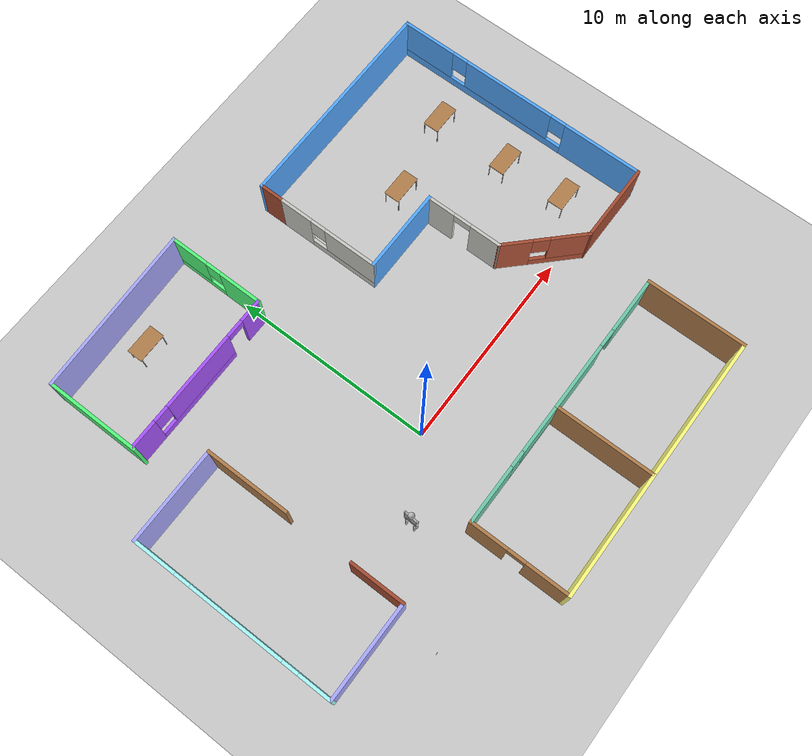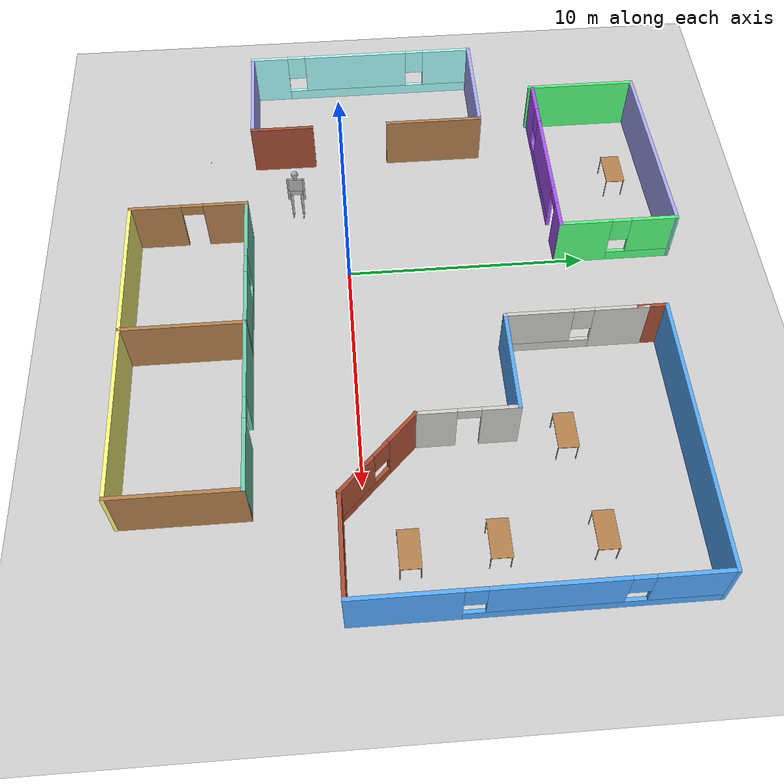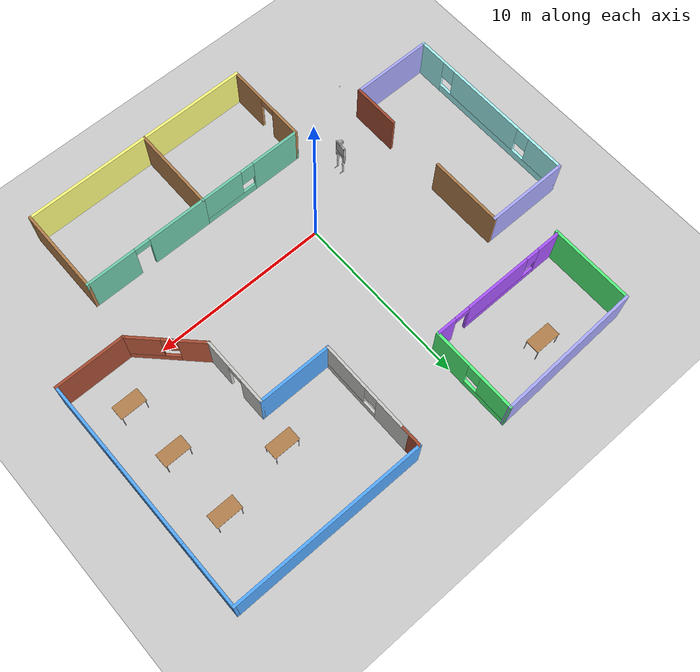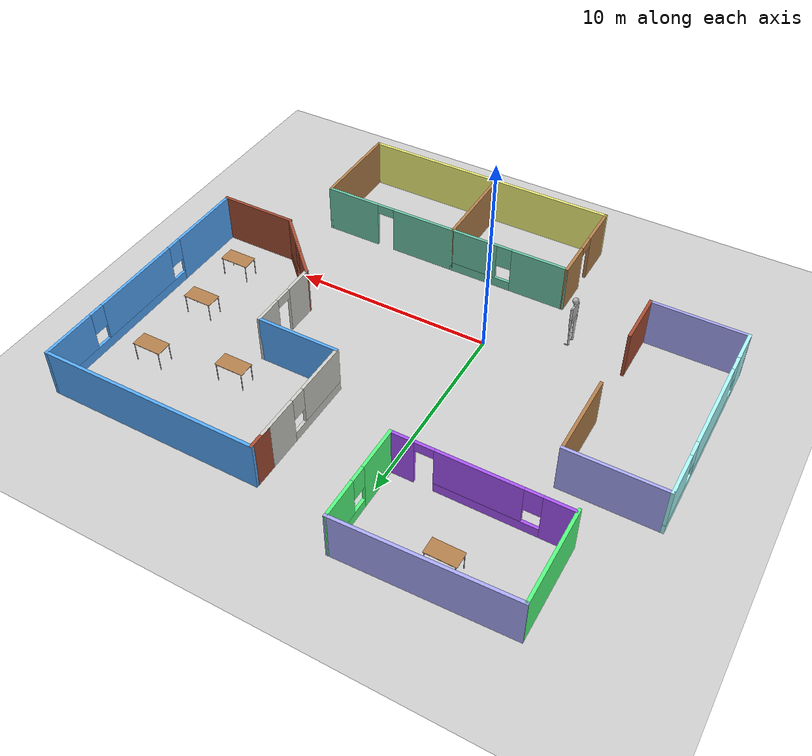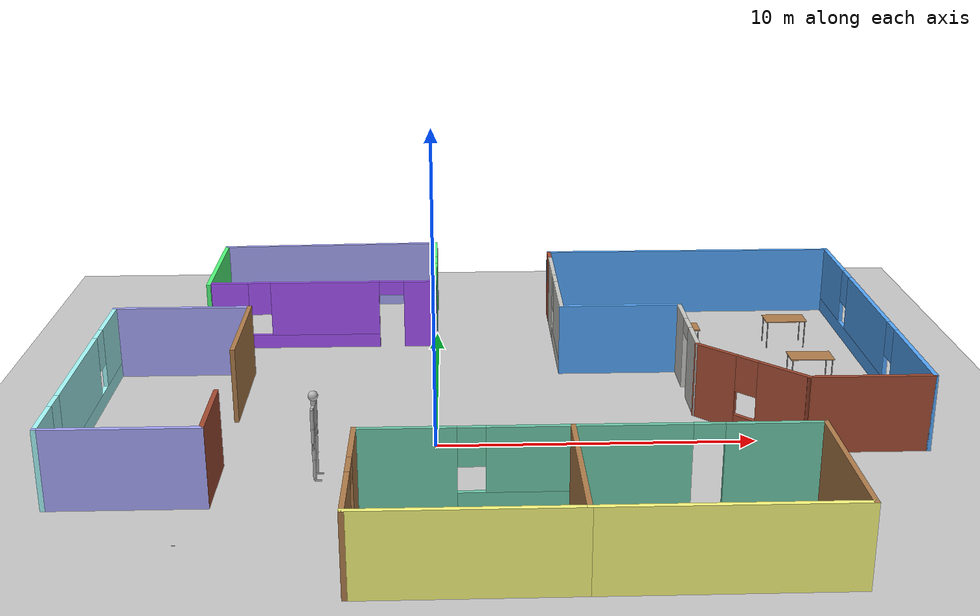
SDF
<sdf version="1.6">
 <world name="default">
  <light name="sun" type="directional">
   <pose>0 0 10 0 -0 0</pose>
   <diffuse>0.8 0.8 0.8 1</diffuse>
   <specular>0.2 0.2 0.2 1</specular>
   <attenuation>
    <range>1000</range>
    <constant>0.9</constant>
    <linear>0.01</linear>
    <quadratic>0.001</quadratic>
   </attenuation>
   <direction>-0.5 0.1 -0.9</direction>
  </light>
  <model name="ground_plane">
   <static>1</static>
   <link name="link">
    <collision name="collision">
     <geometry><plane><normal>0 0 1</normal><size>100 100</size></plane></geometry>
     <surface>
      <contact><collide_bitmask>65535</collide_bitmask></contact>
      <friction><ode><mu>100</mu><mu2>50</mu2></ode></friction>
     </surface>
    </collision>
    <visual name="visual">
     <cast_shadows>0</cast_shadows>
     <geometry><plane><normal>0 0 1</normal><size>100 100</size></plane></geometry>
     <material>
      <script><uri>file://media/materials/scripts/gazebo.material</uri><name>Gazebo/Grey</name></script>
     </material>
    </visual>
   </link>
  </model>
  <gravity>0 0 -9.8</gravity>
  <magnetic_field>6e-06 2.3e-05 -4.2e-05</magnetic_field>
  <atmosphere type="adiabatic"/>
  <physics name="default_physics" default="0" type="ode">
   <max_step_size>0.001</max_step_size>
   <real_time_factor>1</real_time_factor>
   <real_time_update_rate>1000</real_time_update_rate>
  </physics>
  <scene><ambient>0.4 0.4 0.4 1</ambient><background>0.7 0.7 0.7 1</background><shadows>1</shadows></scene>
  <spherical_coordinates>
   <surface_model>EARTH_WGS84</surface_model>
   <latitude_deg>0</latitude_deg>
   <longitude_deg>0</longitude_deg>
   <elevation>0</elevation>
   <heading_deg>0</heading_deg>
  </spherical_coordinates>
  <model name="project_world">
   <pose>2.07578 2.357 0 0 -0 0</pose>
   <link name="Wall_1">
    <pose>-1.23578 -6.487 0 0 -0 0</pose>
    <visual name="Wall_1_Visual_0">
     <pose>-1.65552 0 1.25 0 -0 0</pose>
     <geometry><box><size>2.93896 0.15 2.5</size></box></geometry>
     <material>
      <script><uri>file://media/materials/scripts/gazebo.material</uri><name>Gazebo/Grey</name></script>
      <ambient>0.435294 0.796078 0.67451 1</ambient>
     </material>
     <meta><layer>0</layer></meta>
    </visual>
    <collision name="Wall_1_Collision_0">
     <geometry><box><size>2.93896 0.15 2.5</size></box></geometry>
     <pose>-1.65552 0 1.25 0 -0 0</pose>
    </collision>
    <visual name="Wall_1_Visual_1">
     <pose>1.46948 0 0.25 0 -0 0</pose>
     <geometry><box><size>3.31104 0.15 0.5</size></box></geometry>
     <material>
      <script><uri>file://media/materials/scripts/gazebo.material</uri><name>Gazebo/Grey</name></script>
      <ambient>0.435294 0.796078 0.67451 1</ambient>
     </material>
     <meta><layer>0</layer></meta>
    </visual>
    <collision name="Wall_1_Collision_1">
     <geometry><box><size>3.31104 0.15 0.5</size></box></geometry>
     <pose>1.46948 0 0.25 0 -0 0</pose>
    </collision>
    <visual name="Wall_1_Visual_2">
     <pose>1.86948 0 1.5 0 -0 0</pose>
     <geometry><box><size>2.51104 0.15 2</size></box></geometry>
     <material>
      <script><uri>file://media/materials/scripts/gazebo.material</uri><name>Gazebo/Grey</name></script>
      <ambient>0.435294 0.796078 0.67451 1</ambient>
     </material>
     <meta><layer>0</layer></meta>
    </visual>
    <collision name="Wall_1_Collision_2">
     <geometry><box><size>2.51104 0.15 2</size></box></geometry>
     <pose>1.86948 0 1.5 0 -0 0</pose>
    </collision>
    <visual name="Wall_1_Visual_3">
     <pose>0.213964 0 1.9 0 -0 0</pose>
     <geometry><box><size>0.8 0.15 1.2</size></box></geometry>
     <material>
      <script><uri>file://media/materials/scripts/gazebo.material</uri><name>Gazebo/Grey</name></script>
      <ambient>0.435294 0.796078 0.67451 1</ambient>
     </material>
     <meta><layer>0</layer></meta>
    </visual>
    <collision name="Wall_1_Collision_3">
     <geometry><box><size>0.8 0.15 1.2</size></box></geometry>
     <pose>0.213964 0 1.9 0 -0 0</pose>
    </collision>
   </link>
   <link name="Wall_11">
    <collision name="Wall_11_Collision">
     <geometry><box><size>2.75 0.15 2.5</size></box></geometry>
     <pose>0 0 1.25 0 -0 0</pose>
    </collision>
    <visual name="Wall_11_Visual">
     <pose>0 0 1.25 0 -0 0</pose>
     <geometry><box><size>2.75 0.15 2.5</size></box></geometry>
     <material>
      <script><uri>file://media/materials/scripts/gazebo.material</uri><name>Gazebo/Bricks</name></script>
      <ambient>1 1 1 1</ambient>
     </material>
     <meta><layer>0</layer></meta>
    </visual>
    <pose>-8.5094 -4.95184 0 0 -0 1.5708</pose>
   </link>
   <link name="Wall_13">
    <pose>-6.18981 6.48446 0 0 -0 0</pose>
    <visual name="Wall_13_Visual_0">
     <pose>-3.41981 0 1.25 0 -0 0</pose>
     <geometry><box><size>1.41037 0.15 2.5</size></box></geometry>
     <material>
      <script><uri>file://media/materials/scripts/gazebo.material</uri><name>Gazebo/Grey</name></script>
      <ambient>0.666667 0.333333 1 1</ambient>
     </material>
     <meta><layer>0</layer></meta>
    </visual>
    <collision name="Wall_13_Collision_0">
     <geometry><box><size>1.41037 0.15 2.5</size></box></geometry>
     <pose>-3.41981 0 1.25 0 -0 0</pose>
    </collision>
    <visual name="Wall_13_Visual_1">
     <pose>3.52234 0 1.25 0 -0 0</pose>
     <geometry><box><size>1.20531 0.15 2.5</size></box></geometry>
     <material>
      <script><uri>file://media/materials/scripts/gazebo.material</uri><name>Gazebo/Grey</name></script>
      <ambient>0.666667 0.333333 1 1</ambient>
     </material>
     <meta><layer>0</layer></meta>
    </visual>
    <collision name="Wall_13_Collision_1">
     <geometry><box><size>1.20531 0.15 2.5</size></box></geometry>
     <pose>3.52234 0 1.25 0 -0 0</pose>
    </collision>
    <visual name="Wall_13_Visual_2">
     <pose>-0.34747 0 0.25 0 -0 0</pose>
     <geometry><box><size>4.73431 0.15 0.5</size></box></geometry>
     <material>
      <script><uri>file://media/materials/scripts/gazebo.material</uri><name>Gazebo/Grey</name></script>
      <ambient>0.666667 0.333333 1 1</ambient>
     </material>
     <meta><layer>0</layer></meta>
    </visual>
    <collision name="Wall_13_Collision_2">
     <geometry><box><size>4.73431 0.15 0.5</size></box></geometry>
     <pose>-0.34747 0 0.25 0 -0 0</pose>
    </collision>
    <visual name="Wall_13_Visual_3">
     <pose>0.05253 0 1.5 0 -0 0</pose>
     <geometry><box><size>3.93431 0.15 2</size></box></geometry>
     <material>
      <script><uri>file://media/materials/scripts/gazebo.material</uri><name>Gazebo/Grey</name></script>
      <ambient>0.666667 0.333333 1 1</ambient>
     </material>
     <meta><layer>0</layer></meta>
    </visual>
    <collision name="Wall_13_Collision_3">
     <geometry><box><size>3.93431 0.15 2</size></box></geometry>
     <pose>0.05253 0 1.5 0 -0 0</pose>
    </collision>
    <visual name="Wall_13_Visual_4">
     <pose>-2.31463 0 1.9 0 -0 0</pose>
     <geometry><box><size>0.8 0.15 1.2</size></box></geometry>
     <material>
      <script><uri>file://media/materials/scripts/gazebo.material</uri><name>Gazebo/Grey</name></script>
      <ambient>0.666667 0.333333 1 1</ambient>
     </material>
     <meta><layer>0</layer></meta>
    </visual>
    <collision name="Wall_13_Collision_4">
     <geometry><box><size>0.8 0.15 1.2</size></box></geometry>
     <pose>-2.31463 0 1.9 0 -0 0</pose>
    </collision>
    <visual name="Wall_13_Visual_5">
     <pose>2.46969 0 2.25 0 -0 0</pose>
     <geometry><box><size>0.9 0.15 0.5</size></box></geometry>
     <material>
      <script><uri>file://media/materials/scripts/gazebo.material</uri><name>Gazebo/Grey</name></script>
      <ambient>0.666667 0.333333 1 1</ambient>
     </material>
     <meta><layer>0</layer></meta>
    </visual>
    <collision name="Wall_13_Collision_5">
     <geometry><box><size>0.9 0.15 0.5</size></box></geometry>
     <pose>2.46969 0 2.25 0 -0 0</pose>
    </collision>
   </link>
   <link name="Wall_14">
    <pose>-2.13981 8.90946 0 0 -0 1.5708</pose>
    <visual name="Wall_14_Visual_0">
     <pose>-1.38846 0 1.25 0 -0 0</pose>
     <geometry><box><size>2.22308 0.15 2.5</size></box></geometry>
     <material>
      <script><uri>file://media/materials/scripts/gazebo.material</uri><name>Gazebo/Grey</name></script>
      <ambient>0.333333 1 0.498039 1</ambient>
     </material>
     <meta><layer>0</layer></meta>
    </visual>
    <collision name="Wall_14_Collision_0">
     <geometry><box><size>2.22308 0.15 2.5</size></box></geometry>
     <pose>-1.38846 0 1.25 0 -0 0</pose>
    </collision>
    <visual name="Wall_14_Visual_1">
     <pose>1.11154 0 0.25 0 -0 0</pose>
     <geometry><box><size>2.77692 0.15 0.5</size></box></geometry>
     <material>
      <script><uri>file://media/materials/scripts/gazebo.material</uri><name>Gazebo/Grey</name></script>
      <ambient>0.333333 1 0.498039 1</ambient>
     </material>
     <meta><layer>0</layer></meta>
    </visual>
    <collision name="Wall_14_Collision_1">
     <geometry><box><size>2.77692 0.15 0.5</size></box></geometry>
     <pose>1.11154 0 0.25 0 -0 0</pose>
    </collision>
    <visual name="Wall_14_Visual_2">
     <pose>1.51154 0 1.5 0 -0 0</pose>
     <geometry><box><size>1.97692 0.15 2</size></box></geometry>
     <material>
      <script><uri>file://media/materials/scripts/gazebo.material</uri><name>Gazebo/Grey</name></script>
      <ambient>0.333333 1 0.498039 1</ambient>
     </material>
     <meta><layer>0</layer></meta>
    </visual>
    <collision name="Wall_14_Collision_2">
     <geometry><box><size>1.97692 0.15 2</size></box></geometry>
     <pose>1.51154 0 1.5 0 -0 0</pose>
    </collision>
    <visual name="Wall_14_Visual_3">
     <pose>0.123076 0 1.9 0 -0 0</pose>
     <geometry><box><size>0.8 0.15 1.2</size></box></geometry>
     <material>
      <script><uri>file://media/materials/scripts/gazebo.material</uri><name>Gazebo/Grey</name></script>
      <ambient>0.333333 1 0.498039 1</ambient>
     </material>
     <meta><layer>0</layer></meta>
    </visual>
    <collision name="Wall_14_Collision_3">
     <geometry><box><size>0.8 0.15 1.2</size></box></geometry>
     <pose>0.123076 0 1.9 0 -0 0</pose>
    </collision>
   </link>
   <link name="Wall_15">
    <collision name="Wall_15_Collision">
     <geometry><box><size>8.3252 0.15 2.5</size></box></geometry>
     <pose>0 0 1.25 0 -0 0</pose>
    </collision>
    <visual name="Wall_15_Visual">
     <pose>0 0 1.25 0 -0 0</pose>
     <geometry><box><size>8.3252 0.15 2.5</size></box></geometry>
     <material>
      <script><uri>file://media/materials/scripts/gazebo.material</uri><name>Gazebo/Grey</name></script>
      <ambient>0.666667 0.666667 1 1</ambient>
     </material>
     <meta><layer>0</layer></meta>
    </visual>
    <pose>-6.22499 11.1937 0 0 0 -3.10716</pose>
   </link>
   <link name="Wall_16">
    <collision name="Wall_16_Collision">
     <geometry><box><size>4.75 0.15 2.5</size></box></geometry>
     <pose>0 0 1.25 0 -0 0</pose>
    </collision>
    <visual name="Wall_16_Visual">
     <pose>0 0 1.25 0 -0 0</pose>
     <geometry><box><size>4.75 0.15 2.5</size></box></geometry>
     <material>
      <script><uri>file://media/materials/scripts/gazebo.material</uri><name>Gazebo/Grey</name></script>
      <ambient>0.333333 1 0.498039 1</ambient>
     </material>
     <meta><layer>0</layer></meta>
    </visual>
    <pose>-10.3102 8.68268 0 0 0 -1.5708</pose>
   </link>
   <link name="Wall_18">
    <pose>5.36422 -6.487 0 0 -0 0</pose>
    <visual name="Wall_18_Visual_0">
     <pose>-1.90549 0 1.25 0 -0 0</pose>
     <geometry><box><size>3.43901 0.15 2.5</size></box></geometry>
     <material>
      <script><uri>file://media/materials/scripts/gazebo.material</uri><name>Gazebo/Grey</name></script>
      <ambient>0.435294 0.796078 0.67451 1</ambient>
     </material>
     <meta><layer>0</layer></meta>
    </visual>
    <collision name="Wall_18_Collision_0">
     <geometry><box><size>3.43901 0.15 2.5</size></box></geometry>
     <pose>-1.90549 0 1.25 0 -0 0</pose>
    </collision>
    <visual name="Wall_18_Visual_1">
     <pose>2.16951 0 1.25 0 -0 0</pose>
     <geometry><box><size>2.91099 0.15 2.5</size></box></geometry>
     <material>
      <script><uri>file://media/materials/scripts/gazebo.material</uri><name>Gazebo/Grey</name></script>
      <ambient>0.435294 0.796078 0.67451 1</ambient>
     </material>
     <meta><layer>0</layer></meta>
    </visual>
    <collision name="Wall_18_Collision_1">
     <geometry><box><size>2.91099 0.15 2.5</size></box></geometry>
     <pose>2.16951 0 1.25 0 -0 0</pose>
    </collision>
    <visual name="Wall_18_Visual_2">
     <pose>0.264014 0 2.25 0 -0 0</pose>
     <geometry><box><size>0.9 0.15 0.5</size></box></geometry>
     <material>
      <script><uri>file://media/materials/scripts/gazebo.material</uri><name>Gazebo/Grey</name></script>
      <ambient>0.435294 0.796078 0.67451 1</ambient>
     </material>
     <meta><layer>0</layer></meta>
    </visual>
    <collision name="Wall_18_Collision_2">
     <geometry><box><size>0.9 0.15 0.5</size></box></geometry>
     <pose>0.264014 0 2.25 0 -0 0</pose>
    </collision>
   </link>
   <link name="Wall_19">
    <collision name="Wall_19_Collision">
     <geometry><box><size>5 0.15 2.5</size></box></geometry>
     <pose>0 0 1.25 0 -0 0</pose>
    </collision>
    <visual name="Wall_19_Visual">
     <pose>0 0 1.25 0 -0 0</pose>
     <geometry><box><size>5 0.15 2.5</size></box></geometry>
     <material>
      <script><uri>file://media/materials/scripts/gazebo.material</uri><name>Gazebo/Wood</name></script>
      <ambient>1 1 1 1</ambient>
     </material>
     <meta><layer>0</layer></meta>
    </visual>
    <pose>8.91422 -8.912 0 0 0 -1.5708</pose>
   </link>
   <link name="Wall_2">
    <collision name="Wall_2_Collision">
     <geometry><box><size>5 0.15 2.5</size></box></geometry>
     <pose>0 0 1.25 0 -0 0</pose>
    </collision>
    <visual name="Wall_2_Visual">
     <pose>0 0 1.25 0 -0 0</pose>
     <geometry><box><size>5 0.15 2.5</size></box></geometry>
     <material>
      <script><uri>file://media/materials/scripts/gazebo.material</uri><name>Gazebo/Wood</name></script>
      <ambient>1 1 1 1</ambient>
     </material>
     <meta><layer>0</layer></meta>
    </visual>
    <pose>1.81422 -8.912 0 0 0 -1.5708</pose>
   </link>
   <link name="Wall_20">
    <collision name="Wall_20_Collision">
     <geometry><box><size>7.25 0.15 2.5</size></box></geometry>
     <pose>0 0 1.25 0 -0 0</pose>
    </collision>
    <visual name="Wall_20_Visual">
     <pose>0 0 1.25 0 -0 0</pose>
     <geometry><box><size>7.25 0.15 2.5</size></box></geometry>
     <material>
      <script><uri>file://media/materials/scripts/gazebo.material</uri><name>Gazebo/Grey</name></script>
      <ambient>1 1 0.498039 1</ambient>
     </material>
     <meta><layer>0</layer></meta>
    </visual>
    <pose>5.36422 -11.337 0 0 -0 3.14159</pose>
   </link>
   <link name="Wall_22">
    <pose>2.26026 6.37326 0 0 0 -1.5708</pose>
    <visual name="Wall_22_Visual_0">
     <pose>-1.78632 0 1.25 0 -0 0</pose>
     <geometry><box><size>2.17736 0.15 2.5</size></box></geometry>
     <material>
      <script><uri>file://media/materials/scripts/gazebo.material</uri><name>Gazebo/CeilingTiled</name></script>
      <ambient>1 0.666667 1 1</ambient>
     </material>
     <meta><layer>0</layer></meta>
    </visual>
    <collision name="Wall_22_Collision_0">
     <geometry><box><size>2.17736 0.15 2.5</size></box></geometry>
     <pose>-1.78632 0 1.25 0 -0 0</pose>
    </collision>
    <visual name="Wall_22_Visual_1">
     <pose>1.08868 0 0.25 0 -0 0</pose>
     <geometry><box><size>3.57264 0.15 0.5</size></box></geometry>
     <material>
      <script><uri>file://media/materials/scripts/gazebo.material</uri><name>Gazebo/CeilingTiled</name></script>
      <ambient>1 0.666667 1 1</ambient>
     </material>
     <meta><layer>0</layer></meta>
    </visual>
    <collision name="Wall_22_Collision_1">
     <geometry><box><size>3.57264 0.15 0.5</size></box></geometry>
     <pose>1.08868 0 0.25 0 -0 0</pose>
    </collision>
    <visual name="Wall_22_Visual_2">
     <pose>1.48868 0 1.5 0 -0 0</pose>
     <geometry><box><size>2.77264 0.15 2</size></box></geometry>
     <material>
      <script><uri>file://media/materials/scripts/gazebo.material</uri><name>Gazebo/CeilingTiled</name></script>
      <ambient>1 0.666667 1 1</ambient>
     </material>
     <meta><layer>0</layer></meta>
    </visual>
    <collision name="Wall_22_Collision_2">
     <geometry><box><size>2.77264 0.15 2</size></box></geometry>
     <pose>1.48868 0 1.5 0 -0 0</pose>
    </collision>
    <visual name="Wall_22_Visual_3">
     <pose>-0.297644 0 1.9 0 -0 0</pose>
     <geometry><box><size>0.8 0.15 1.2</size></box></geometry>
     <material>
      <script><uri>file://media/materials/scripts/gazebo.material</uri><name>Gazebo/CeilingTiled</name></script>
      <ambient>1 0.666667 1 1</ambient>
     </material>
     <meta><layer>0</layer></meta>
    </visual>
    <collision name="Wall_22_Collision_3">
     <geometry><box><size>0.8 0.15 1.2</size></box></geometry>
     <pose>-0.297644 0 1.9 0 -0 0</pose>
    </collision>
   </link>
   <link name="Wall_23">
    <collision name="Wall_23_Collision">
     <geometry><box><size>4.25 0.15 2.5</size></box></geometry>
     <pose>0 0 1.25 0 -0 0</pose>
    </collision>
    <visual name="Wall_23_Visual">
     <pose>0 0 1.25 0 -0 0</pose>
     <geometry><box><size>4.25 0.15 2.5</size></box></geometry>
     <material>
      <script><uri>file://media/materials/scripts/gazebo.material</uri><name>Gazebo/Grey</name></script>
      <ambient>0.333333 0.666667 1 1</ambient>
     </material>
     <meta><layer>0</layer></meta>
    </visual>
    <pose>4.31026 3.57326 0 0 -0 0</pose>
   </link>
   <link name="Wall_24">
    <pose>6.36026 1.64826 0 0 0 -1.5708</pose>
    <visual name="Wall_24_Visual_0">
     <pose>-1.25855 0 1.25 0 -0 0</pose>
     <geometry><box><size>1.4829 0.15 2.5</size></box></geometry>
     <material>
      <script><uri>file://media/materials/scripts/gazebo.material</uri><name>Gazebo/CeilingTiled</name></script>
      <ambient>0.760784 0.662745 0.627451 1</ambient>
     </material>
     <meta><layer>0</layer></meta>
    </visual>
    <collision name="Wall_24_Collision_0">
     <geometry><box><size>1.4829 0.15 2.5</size></box></geometry>
     <pose>-1.25855 0 1.25 0 -0 0</pose>
    </collision>
    <visual name="Wall_24_Visual_1">
     <pose>1.19145 0 1.25 0 -0 0</pose>
     <geometry><box><size>1.6171 0.15 2.5</size></box></geometry>
     <material>
      <script><uri>file://media/materials/scripts/gazebo.material</uri><name>Gazebo/CeilingTiled</name></script>
      <ambient>0.760784 0.662745 0.627451 1</ambient>
     </material>
     <meta><layer>0</layer></meta>
    </visual>
    <collision name="Wall_24_Collision_1">
     <geometry><box><size>1.6171 0.15 2.5</size></box></geometry>
     <pose>1.19145 0 1.25 0 -0 0</pose>
    </collision>
    <visual name="Wall_24_Visual_2">
     <pose>-0.067102 0 2.25 0 -0 0</pose>
     <geometry><box><size>0.9 0.15 0.5</size></box></geometry>
     <material>
      <script><uri>file://media/materials/scripts/gazebo.material</uri><name>Gazebo/CeilingTiled</name></script>
      <ambient>0.760784 0.662745 0.627451 1</ambient>
     </material>
     <meta><layer>0</layer></meta>
    </visual>
    <collision name="Wall_24_Collision_2">
     <geometry><box><size>0.9 0.15 0.5</size></box></geometry>
     <pose>-0.067102 0 2.25 0 -0 0</pose>
    </collision>
   </link>
   <link name="Wall_25">
    <pose>7.80983 -1.72631 0 0 0 -0.785398</pose>
    <visual name="Wall_25_Visual_0">
     <pose>-1.33199 0 1.25 0 -0 0</pose>
     <geometry><box><size>1.58602 0.15 2.5</size></box></geometry>
     <material>
      <script><uri>file://media/materials/scripts/gazebo.material</uri><name>Gazebo/Bricks</name></script>
      <ambient>1 1 1 1</ambient>
     </material>
     <meta><layer>0</layer></meta>
    </visual>
    <collision name="Wall_25_Collision_0">
     <geometry><box><size>1.58602 0.15 2.5</size></box></geometry>
     <pose>-1.33199 0 1.25 0 -0 0</pose>
    </collision>
    <visual name="Wall_25_Visual_1">
     <pose>0.793009 0 0.25 0 -0 0</pose>
     <geometry><box><size>2.66398 0.15 0.5</size></box></geometry>
     <material>
      <script><uri>file://media/materials/scripts/gazebo.material</uri><name>Gazebo/Bricks</name></script>
      <ambient>1 1 1 1</ambient>
     </material>
     <meta><layer>0</layer></meta>
    </visual>
    <collision name="Wall_25_Collision_1">
     <geometry><box><size>2.66398 0.15 0.5</size></box></geometry>
     <pose>0.793009 0 0.25 0 -0 0</pose>
    </collision>
    <visual name="Wall_25_Visual_2">
     <pose>1.19301 0 1.5 0 -0 0</pose>
     <geometry><box><size>1.86398 0.15 2</size></box></geometry>
     <material>
      <script><uri>file://media/materials/scripts/gazebo.material</uri><name>Gazebo/Bricks</name></script>
      <ambient>1 1 1 1</ambient>
     </material>
     <meta><layer>0</layer></meta>
    </visual>
    <collision name="Wall_25_Collision_2">
     <geometry><box><size>1.86398 0.15 2</size></box></geometry>
     <pose>1.19301 0 1.5 0 -0 0</pose>
    </collision>
    <visual name="Wall_25_Visual_3">
     <pose>-0.138981 0 1.9 0 -0 0</pose>
     <geometry><box><size>0.8 0.15 1.2</size></box></geometry>
     <material>
      <script><uri>file://media/materials/scripts/gazebo.material</uri><name>Gazebo/Bricks</name></script>
      <ambient>1 1 1 1</ambient>
     </material>
     <meta><layer>0</layer></meta>
    </visual>
    <collision name="Wall_25_Collision_3">
     <geometry><box><size>0.8 0.15 1.2</size></box></geometry>
     <pose>-0.138981 0 1.9 0 -0 0</pose>
    </collision>
   </link>
   <link name="Wall_26">
    <collision name="Wall_26_Collision">
     <geometry><box><size>4 0.15 2.5</size></box></geometry>
     <pose>0 0 1.25 0 -0 0</pose>
    </collision>
    <visual name="Wall_26_Visual">
     <pose>0 0 1.25 0 -0 0</pose>
     <geometry><box><size>4 0.15 2.5</size></box></geometry>
     <material>
      <script><uri>file://media/materials/scripts/gazebo.material</uri><name>Gazebo/Bricks</name></script>
      <ambient>1 1 1 1</ambient>
     </material>
     <meta><layer>0</layer></meta>
    </visual>
    <pose>11.1844 -3.17588 0 0 -0 0</pose>
   </link>
   <link name="Wall_27">
    <pose>13.1094 3.37412 0 0 -0 1.5708</pose>
    <visual name="Wall_27_Visual_0">
     <pose>-4.60393 0 1.25 0 -0 0</pose>
     <geometry><box><size>4.04214 0.15 2.5</size></box></geometry>
     <material>
      <script><uri>file://media/materials/scripts/gazebo.material</uri><name>Gazebo/Grey</name></script>
      <ambient>0.333333 0.666667 1 1</ambient>
     </material>
     <meta><layer>0</layer></meta>
    </visual>
    <collision name="Wall_27_Collision_0">
     <geometry><box><size>4.04214 0.15 2.5</size></box></geometry>
     <pose>-4.60393 0 1.25 0 -0 0</pose>
    </collision>
    <visual name="Wall_27_Visual_1">
     <pose>2.02107 0 0.25 0 -0 0</pose>
     <geometry><box><size>9.20786 0.15 0.5</size></box></geometry>
     <material>
      <script><uri>file://media/materials/scripts/gazebo.material</uri><name>Gazebo/Grey</name></script>
      <ambient>0.333333 0.666667 1 1</ambient>
     </material>
     <meta><layer>0</layer></meta>
    </visual>
    <collision name="Wall_27_Collision_1">
     <geometry><box><size>9.20786 0.15 0.5</size></box></geometry>
     <pose>2.02107 0 0.25 0 -0 0</pose>
    </collision>
    <visual name="Wall_27_Visual_2">
     <pose>0.610161 0 1.5 0 -0 0</pose>
     <geometry><box><size>4.78604 0.15 2</size></box></geometry>
     <material>
      <script><uri>file://media/materials/scripts/gazebo.material</uri><name>Gazebo/Grey</name></script>
      <ambient>0.333333 0.666667 1 1</ambient>
     </material>
     <meta><layer>0</layer></meta>
    </visual>
    <collision name="Wall_27_Collision_2">
     <geometry><box><size>4.78604 0.15 2</size></box></geometry>
     <pose>0.610161 0 1.5 0 -0 0</pose>
    </collision>
    <visual name="Wall_27_Visual_3">
     <pose>5.21409 0 1.5 0 -0 0</pose>
     <geometry><box><size>2.82182 0.15 2</size></box></geometry>
     <material>
      <script><uri>file://media/materials/scripts/gazebo.material</uri><name>Gazebo/Grey</name></script>
      <ambient>0.333333 0.666667 1 1</ambient>
     </material>
     <meta><layer>0</layer></meta>
    </visual>
    <collision name="Wall_27_Collision_3">
     <geometry><box><size>2.82182 0.15 2</size></box></geometry>
     <pose>5.21409 0 1.5 0 -0 0</pose>
    </collision>
    <visual name="Wall_27_Visual_4">
     <pose>-2.18286 0 1.9 0 -0 0</pose>
     <geometry><box><size>0.8 0.15 1.2</size></box></geometry>
     <material>
      <script><uri>file://media/materials/scripts/gazebo.material</uri><name>Gazebo/Grey</name></script>
      <ambient>0.333333 0.666667 1 1</ambient>
     </material>
     <meta><layer>0</layer></meta>
    </visual>
    <collision name="Wall_27_Collision_4">
     <geometry><box><size>0.8 0.15 1.2</size></box></geometry>
     <pose>-2.18286 0 1.9 0 -0 0</pose>
    </collision>
    <visual name="Wall_27_Visual_5">
     <pose>3.40318 0 1.9 0 -0 0</pose>
     <geometry><box><size>0.8 0.15 1.2</size></box></geometry>
     <material>
      <script><uri>file://media/materials/scripts/gazebo.material</uri><name>Gazebo/Grey</name></script>
      <ambient>0.333333 0.666667 1 1</ambient>
     </material>
     <meta><layer>0</layer></meta>
    </visual>
    <collision name="Wall_27_Collision_5">
     <geometry><box><size>0.8 0.15 1.2</size></box></geometry>
     <pose>3.40318 0 1.9 0 -0 0</pose>
    </collision>
   </link>
   <link name="Wall_28">
    <collision name="Wall_28_Collision">
     <geometry><box><size>11 0.15 2.5</size></box></geometry>
     <pose>0 0 1.25 0 -0 0</pose>
    </collision>
    <visual name="Wall_28_Visual">
     <pose>0 0 1.25 0 -0 0</pose>
     <geometry><box><size>11 0.15 2.5</size></box></geometry>
     <material>
      <script><uri>file://media/materials/scripts/gazebo.material</uri><name>Gazebo/Grey</name></script>
      <ambient>0.333333 0.666667 1 1</ambient>
     </material>
     <meta><layer>0</layer></meta>
    </visual>
    <pose>7.6844 9.92412 0 0 -0 3.14159</pose>
   </link>
   <link name="Wall_29">
    <collision name="Wall_29_Collision">
     <geometry><box><size>1.25 0.15 2.5</size></box></geometry>
     <pose>0 0 1.25 0 -0 0</pose>
    </collision>
    <visual name="Wall_29_Visual">
     <pose>0 0 1.25 0 -0 0</pose>
     <geometry><box><size>1.25 0.15 2.5</size></box></geometry>
     <material>
      <script><uri>file://media/materials/scripts/gazebo.material</uri><name>Gazebo/Bricks</name></script>
      <ambient>1 1 1 1</ambient>
     </material>
     <meta><layer>0</layer></meta>
    </visual>
    <pose>2.2594 9.37412 0 0 0 -1.5708</pose>
   </link>
   <link name="Wall_3">
    <collision name="Wall_3_Collision">
     <geometry><box><size>6.25 0.15 2.5</size></box></geometry>
     <pose>0 0 1.25 0 -0 0</pose>
    </collision>
    <visual name="Wall_3_Visual">
     <pose>0 0 1.25 0 -0 0</pose>
     <geometry><box><size>6.25 0.15 2.5</size></box></geometry>
     <material>
      <script><uri>file://media/materials/scripts/gazebo.material</uri><name>Gazebo/Grey</name></script>
      <ambient>1 1 0.498039 1</ambient>
     </material>
     <meta><layer>0</layer></meta>
    </visual>
    <pose>-1.23578 -11.337 0 0 -0 3.14159</pose>
   </link>
   <link name="Wall_4">
    <pose>-4.28578 -8.912 0 0 -0 1.5708</pose>
    <visual name="Wall_4_Visual_0">
     <pose>-1.39761 0 1.25 0 -0 0</pose>
     <geometry><box><size>2.20478 0.15 2.5</size></box></geometry>
     <material>
      <script><uri>file://media/materials/scripts/gazebo.material</uri><name>Gazebo/Wood</name></script>
      <ambient>1 1 1 1</ambient>
     </material>
     <meta><layer>0</layer></meta>
    </visual>
    <collision name="Wall_4_Collision_0">
     <geometry><box><size>2.20478 0.15 2.5</size></box></geometry>
     <pose>-1.39761 0 1.25 0 -0 0</pose>
    </collision>
    <visual name="Wall_4_Visual_1">
     <pose>1.55239 0 1.25 0 -0 0</pose>
     <geometry><box><size>1.89522 0.15 2.5</size></box></geometry>
     <material>
      <script><uri>file://media/materials/scripts/gazebo.material</uri><name>Gazebo/Wood</name></script>
      <ambient>1 1 1 1</ambient>
     </material>
     <meta><layer>0</layer></meta>
    </visual>
    <collision name="Wall_4_Collision_1">
     <geometry><box><size>1.89522 0.15 2.5</size></box></geometry>
     <pose>1.55239 0 1.25 0 -0 0</pose>
    </collision>
    <visual name="Wall_4_Visual_2">
     <pose>0.154783 0 2.25 0 -0 0</pose>
     <geometry><box><size>0.9 0.15 0.5</size></box></geometry>
     <material>
      <script><uri>file://media/materials/scripts/gazebo.material</uri><name>Gazebo/Wood</name></script>
      <ambient>1 1 1 1</ambient>
     </material>
     <meta><layer>0</layer></meta>
    </visual>
    <collision name="Wall_4_Collision_2">
     <geometry><box><size>0.9 0.15 0.5</size></box></geometry>
     <pose>0.154783 0 2.25 0 -0 0</pose>
    </collision>
   </link>
   <link name="Wall_6">
    <collision name="Wall_6_Collision">
     <geometry><box><size>4.75 0.15 2.5</size></box></geometry>
     <pose>0 0 1.25 0 -0 0</pose>
    </collision>
    <visual name="Wall_6_Visual">
     <pose>0 0 1.25 0 -0 0</pose>
     <geometry><box><size>4.75 0.15 2.5</size></box></geometry>
     <material>
      <script><uri>file://media/materials/scripts/gazebo.material</uri><name>Gazebo/Grey</name></script>
      <ambient>0.666667 0.666667 1 1</ambient>
     </material>
     <meta><layer>0</layer></meta>
    </visual>
    <pose>-10.8094 -6.25184 0 0 -0 3.14159</pose>
   </link>
   <link name="Wall_7">
    <pose>-13.1094 -1.20184 0 0 -0 1.5708</pose>
    <visual name="Wall_7_Visual_0">
     <pose>-4.27917 0 1.25 0 -0 0</pose>
     <geometry><box><size>1.69166 0.15 2.5</size></box></geometry>
     <material>
      <script><uri>file://media/materials/scripts/gazebo.material</uri><name>Gazebo/Grey</name></script>
      <ambient>0.666667 1 1 1</ambient>
     </material>
     <meta><layer>0</layer></meta>
    </visual>
    <collision name="Wall_7_Collision_0">
     <geometry><box><size>1.69166 0.15 2.5</size></box></geometry>
     <pose>-4.27917 0 1.25 0 -0 0</pose>
    </collision>
    <visual name="Wall_7_Visual_1">
     <pose>0.84583 0 0.25 0 -0 0</pose>
     <geometry><box><size>8.55834 0.15 0.5</size></box></geometry>
     <material>
      <script><uri>file://media/materials/scripts/gazebo.material</uri><name>Gazebo/Grey</name></script>
      <ambient>0.666667 1 1 1</ambient>
     </material>
     <meta><layer>0</layer></meta>
    </visual>
    <collision name="Wall_7_Collision_1">
     <geometry><box><size>8.55834 0.15 0.5</size></box></geometry>
     <pose>0.84583 0 0.25 0 -0 0</pose>
    </collision>
    <visual name="Wall_7_Visual_2">
     <pose>-0.266919 0 1.5 0 -0 0</pose>
     <geometry><box><size>4.73284 0.15 2</size></box></geometry>
     <material>
      <script><uri>file://media/materials/scripts/gazebo.material</uri><name>Gazebo/Grey</name></script>
      <ambient>0.666667 1 1 1</ambient>
     </material>
     <meta><layer>0</layer></meta>
    </visual>
    <collision name="Wall_7_Collision_2">
     <geometry><box><size>4.73284 0.15 2</size></box></geometry>
     <pose>-0.266919 0 1.5 0 -0 0</pose>
    </collision>
    <visual name="Wall_7_Visual_3">
     <pose>4.01225 0 1.5 0 -0 0</pose>
     <geometry><box><size>2.2255 0.15 2</size></box></geometry>
     <material>
      <script><uri>file://media/materials/scripts/gazebo.material</uri><name>Gazebo/Grey</name></script>
      <ambient>0.666667 1 1 1</ambient>
     </material>
     <meta><layer>0</layer></meta>
    </visual>
    <collision name="Wall_7_Collision_3">
     <geometry><box><size>2.2255 0.15 2</size></box></geometry>
     <pose>4.01225 0 1.5 0 -0 0</pose>
    </collision>
    <visual name="Wall_7_Visual_4">
     <pose>-3.03334 0 1.9 0 -0 0</pose>
     <geometry><box><size>0.8 0.15 1.2</size></box></geometry>
     <material>
      <script><uri>file://media/materials/scripts/gazebo.material</uri><name>Gazebo/Grey</name></script>
      <ambient>0.666667 1 1 1</ambient>
     </material>
     <meta><layer>0</layer></meta>
    </visual>
    <collision name="Wall_7_Collision_4">
     <geometry><box><size>0.8 0.15 1.2</size></box></geometry>
     <pose>-3.03334 0 1.9 0 -0 0</pose>
    </collision>
    <visual name="Wall_7_Visual_5">
     <pose>2.4995 0 1.9 0 -0 0</pose>
     <geometry><box><size>0.8 0.15 1.2</size></box></geometry>
     <material>
      <script><uri>file://media/materials/scripts/gazebo.material</uri><name>Gazebo/Grey</name></script>
      <ambient>0.666667 1 1 1</ambient>
     </material>
     <meta><layer>0</layer></meta>
    </visual>
    <collision name="Wall_7_Collision_5">
     <geometry><box><size>0.8 0.15 1.2</size></box></geometry>
     <pose>2.4995 0 1.9 0 -0 0</pose>
    </collision>
   </link>
   <link name="Wall_8">
    <collision name="Wall_8_Collision">
     <geometry><box><size>4.75 0.15 2.5</size></box></geometry>
     <pose>0 0 1.25 0 -0 0</pose>
    </collision>
    <visual name="Wall_8_Visual">
     <pose>0 0 1.25 0 -0 0</pose>
     <geometry><box><size>4.75 0.15 2.5</size></box></geometry>
     <material>
      <script><uri>file://media/materials/scripts/gazebo.material</uri><name>Gazebo/Grey</name></script>
      <ambient>0.666667 0.666667 1 1</ambient>
     </material>
     <meta><layer>0</layer></meta>
    </visual>
    <pose>-10.8094 3.84816 0 0 -0 0</pose>
   </link>
   <link name="Wall_9">
    <collision name="Wall_9_Collision">
     <geometry><box><size>4.25 0.15 2.5</size></box></geometry>
     <pose>0 0 1.25 0 -0 0</pose>
    </collision>
    <visual name="Wall_9_Visual">
     <pose>0 0 1.25 0 -0 0</pose>
     <geometry><box><size>4.25 0.15 2.5</size></box></geometry>
     <material>
      <script><uri>file://media/materials/scripts/gazebo.material</uri><name>Gazebo/Wood</name></script>
      <ambient>1 1 1 1</ambient>
     </material>
     <meta><layer>0</layer></meta>
    </visual>
    <pose>-8.5094 1.79816 0 0 0 -1.5708</pose>
   </link>
   <static>1</static>
  </model>
  <model name="table">
   <static>1</static>
   <link name="link">
    <collision name="surface">
     <pose>0 0 1 0 -0 0</pose>
     <geometry><box><size>1.5 0.8 0.03</size></box></geometry>
     <surface><friction><ode><mu>0.6</mu><mu2>0.6</mu2></ode></friction></surface>
    </collision>
    <visual name="visual1">
     <pose>0 0 1 0 -0 0</pose>
     <geometry><box><size>1.5 0.8 0.03</size></box></geometry>
     <material>
      <script><uri>file://media/materials/scripts/gazebo.material</uri><name>Gazebo/Wood</name></script>
     </material>
    </visual>
    <collision name="front_left_leg">
     <pose>0.68 0.38 0.5 0 -0 0</pose>
     <geometry><cylinder><radius>0.02</radius><length>1</length></cylinder></geometry>
    </collision>
    <visual name="front_left_leg">
     <pose>0.68 0.38 0.5 0 -0 0</pose>
     <geometry><cylinder><radius>0.02</radius><length>1</length></cylinder></geometry>
     <material>
      <script><uri>file://media/materials/scripts/gazebo.material</uri><name>Gazebo/Grey</name></script>
     </material>
    </visual>
    <collision name="front_right_leg">
     <pose>0.68 -0.38 0.5 0 -0 0</pose>
     <geometry><cylinder><radius>0.02</radius><length>1</length></cylinder></geometry>
    </collision>
    <visual name="front_right_leg">
     <pose>0.68 -0.38 0.5 0 -0 0</pose>
     <geometry><cylinder><radius>0.02</radius><length>1</length></cylinder></geometry>
     <material>
      <script><uri>file://media/materials/scripts/gazebo.material</uri><name>Gazebo/Grey</name></script>
     </material>
    </visual>
    <collision name="back_right_leg">
     <pose>-0.68 -0.38 0.5 0 -0 0</pose>
     <geometry><cylinder><radius>0.02</radius><length>1</length></cylinder></geometry>
    </collision>
    <visual name="back_right_leg">
     <pose>-0.68 -0.38 0.5 0 -0 0</pose>
     <geometry><cylinder><radius>0.02</radius><length>1</length></cylinder></geometry>
     <material>
      <script><uri>file://media/materials/scripts/gazebo.material</uri><name>Gazebo/Grey</name></script>
     </material>
    </visual>
    <collision name="back_left_leg">
     <pose>-0.68 0.38 0.5 0 -0 0</pose>
     <geometry><cylinder><radius>0.02</radius><length>1</length></cylinder></geometry>
    </collision>
    <visual name="back_left_leg">
     <pose>-0.68 0.38 0.5 0 -0 0</pose>
     <geometry><cylinder><radius>0.02</radius><length>1</length></cylinder></geometry>
     <material>
      <script><uri>file://media/materials/scripts/gazebo.material</uri><name>Gazebo/Grey</name></script>
     </material>
    </visual>
   </link>
   <pose>12.8261 4.71149 0 0 -0 0</pose>
  </model>
  <model name="table_0">
   <static>1</static>
   <link name="link">
    <collision name="surface">
     <pose>0 0 1 0 -0 0</pose>
     <geometry><box><size>1.5 0.8 0.03</size></box></geometry>
     <surface><friction><ode><mu>0.6</mu><mu2>0.6</mu2></ode></friction></surface>
    </collision>
    <visual name="visual1">
     <pose>0 0 1 0 -0 0</pose>
     <geometry><box><size>1.5 0.8 0.03</size></box></geometry>
     <material>
      <script><uri>file://media/materials/scripts/gazebo.material</uri><name>Gazebo/Wood</name></script>
     </material>
    </visual>
    <collision name="front_left_leg">
     <pose>0.68 0.38 0.5 0 -0 0</pose>
     <geometry><cylinder><radius>0.02</radius><length>1</length></cylinder></geometry>
    </collision>
    <visual name="front_left_leg">
     <pose>0.68 0.38 0.5 0 -0 0</pose>
     <geometry><cylinder><radius>0.02</radius><length>1</length></cylinder></geometry>
     <material>
      <script><uri>file://media/materials/scripts/gazebo.material</uri><name>Gazebo/Grey</name></script>
     </material>
    </visual>
    <collision name="front_right_leg">
     <pose>0.68 -0.38 0.5 0 -0 0</pose>
     <geometry><cylinder><radius>0.02</radius><length>1</length></cylinder></geometry>
    </collision>
    <visual name="front_right_leg">
     <pose>0.68 -0.38 0.5 0 -0 0</pose>
     <geometry><cylinder><radius>0.02</radius><length>1</length></cylinder></geometry>
     <material>
      <script><uri>file://media/materials/scripts/gazebo.material</uri><name>Gazebo/Grey</name></script>
     </material>
    </visual>
    <collision name="back_right_leg">
     <pose>-0.68 -0.38 0.5 0 -0 0</pose>
     <geometry><cylinder><radius>0.02</radius><length>1</length></cylinder></geometry>
    </collision>
    <visual name="back_right_leg">
     <pose>-0.68 -0.38 0.5 0 -0 0</pose>
     <geometry><cylinder><radius>0.02</radius><length>1</length></cylinder></geometry>
     <material>
      <script><uri>file://media/materials/scripts/gazebo.material</uri><name>Gazebo/Grey</name></script>
     </material>
    </visual>
    <collision name="back_left_leg">
     <pose>-0.68 0.38 0.5 0 -0 0</pose>
     <geometry><cylinder><radius>0.02</radius><length>1</length></cylinder></geometry>
    </collision>
    <visual name="back_left_leg">
     <pose>-0.68 0.38 0.5 0 -0 0</pose>
     <geometry><cylinder><radius>0.02</radius><length>1</length></cylinder></geometry>
     <material>
      <script><uri>file://media/materials/scripts/gazebo.material</uri><name>Gazebo/Grey</name></script>
     </material>
    </visual>
   </link>
   <pose>-4.27643 12.0144 0 0 -0 0</pose>
  </model>
  <model name="table_1">
   <static>1</static>
   <link name="link">
    <collision name="surface">
     <pose>0 0 1 0 -0 0</pose>
     <geometry><box><size>1.5 0.8 0.03</size></box></geometry>
     <surface><friction><ode><mu>0.6</mu><mu2>0.6</mu2></ode></friction></surface>
    </collision>
    <visual name="visual1">
     <pose>0 0 1 0 -0 0</pose>
     <geometry><box><size>1.5 0.8 0.03</size></box></geometry>
     <material>
      <script><uri>file://media/materials/scripts/gazebo.material</uri><name>Gazebo/Wood</name></script>
     </material>
    </visual>
    <collision name="front_left_leg">
     <pose>0.68 0.38 0.5 0 -0 0</pose>
     <geometry><cylinder><radius>0.02</radius><length>1</length></cylinder></geometry>
    </collision>
    <visual name="front_left_leg">
     <pose>0.68 0.38 0.5 0 -0 0</pose>
     <geometry><cylinder><radius>0.02</radius><length>1</length></cylinder></geometry>
     <material>
      <script><uri>file://media/materials/scripts/gazebo.material</uri><name>Gazebo/Grey</name></script>
     </material>
    </visual>
    <collision name="front_right_leg">
     <pose>0.68 -0.38 0.5 0 -0 0</pose>
     <geometry><cylinder><radius>0.02</radius><length>1</length></cylinder></geometry>
    </collision>
    <visual name="front_right_leg">
     <pose>0.68 -0.38 0.5 0 -0 0</pose>
     <geometry><cylinder><radius>0.02</radius><length>1</length></cylinder></geometry>
     <material>
      <script><uri>file://media/materials/scripts/gazebo.material</uri><name>Gazebo/Grey</name></script>
     </material>
    </visual>
    <collision name="back_right_leg">
     <pose>-0.68 -0.38 0.5 0 -0 0</pose>
     <geometry><cylinder><radius>0.02</radius><length>1</length></cylinder></geometry>
    </collision>
    <visual name="back_right_leg">
     <pose>-0.68 -0.38 0.5 0 -0 0</pose>
     <geometry><cylinder><radius>0.02</radius><length>1</length></cylinder></geometry>
     <material>
      <script><uri>file://media/materials/scripts/gazebo.material</uri><name>Gazebo/Grey</name></script>
     </material>
    </visual>
    <collision name="back_left_leg">
     <pose>-0.68 0.38 0.5 0 -0 0</pose>
     <geometry><cylinder><radius>0.02</radius><length>1</length></cylinder></geometry>
    </collision>
    <visual name="back_left_leg">
     <pose>-0.68 0.38 0.5 0 -0 0</pose>
     <geometry><cylinder><radius>0.02</radius><length>1</length></cylinder></geometry>
     <material>
      <script><uri>file://media/materials/scripts/gazebo.material</uri><name>Gazebo/Grey</name></script>
     </material>
    </visual>
   </link>
   <pose>12.9896 1.50462 0 0 -0 0</pose>
  </model>
  <model name="table_2">
   <static>1</static>
   <link name="link">
    <collision name="surface">
     <pose>0 0 1 0 -0 0</pose>
     <geometry><box><size>1.5 0.8 0.03</size></box></geometry>
     <surface><friction><ode><mu>0.6</mu><mu2>0.6</mu2></ode></friction></surface>
    </collision>
    <visual name="visual1">
     <pose>0 0 1 0 -0 0</pose>
     <geometry><box><size>1.5 0.8 0.03</size></box></geometry>
     <material>
      <script><uri>file://media/materials/scripts/gazebo.material</uri><name>Gazebo/Wood</name></script>
     </material>
    </visual>
    <collision name="front_left_leg">
     <pose>0.68 0.38 0.5 0 -0 0</pose>
     <geometry><cylinder><radius>0.02</radius><length>1</length></cylinder></geometry>
    </collision>
    <visual name="front_left_leg">
     <pose>0.68 0.38 0.5 0 -0 0</pose>
     <geometry><cylinder><radius>0.02</radius><length>1</length></cylinder></geometry>
     <material>
      <script><uri>file://media/materials/scripts/gazebo.material</uri><name>Gazebo/Grey</name></script>
     </material>
    </visual>
    <collision name="front_right_leg">
     <pose>0.68 -0.38 0.5 0 -0 0</pose>
     <geometry><cylinder><radius>0.02</radius><length>1</length></cylinder></geometry>
    </collision>
    <visual name="front_right_leg">
     <pose>0.68 -0.38 0.5 0 -0 0</pose>
     <geometry><cylinder><radius>0.02</radius><length>1</length></cylinder></geometry>
     <material>
      <script><uri>file://media/materials/scripts/gazebo.material</uri><name>Gazebo/Grey</name></script>
     </material>
    </visual>
    <collision name="back_right_leg">
     <pose>-0.68 -0.38 0.5 0 -0 0</pose>
     <geometry><cylinder><radius>0.02</radius><length>1</length></cylinder></geometry>
    </collision>
    <visual name="back_right_leg">
     <pose>-0.68 -0.38 0.5 0 -0 0</pose>
     <geometry><cylinder><radius>0.02</radius><length>1</length></cylinder></geometry>
     <material>
      <script><uri>file://media/materials/scripts/gazebo.material</uri><name>Gazebo/Grey</name></script>
     </material>
    </visual>
    <collision name="back_left_leg">
     <pose>-0.68 0.38 0.5 0 -0 0</pose>
     <geometry><cylinder><radius>0.02</radius><length>1</length></cylinder></geometry>
    </collision>
    <visual name="back_left_leg">
     <pose>-0.68 0.38 0.5 0 -0 0</pose>
     <geometry><cylinder><radius>0.02</radius><length>1</length></cylinder></geometry>
     <material>
      <script><uri>file://media/materials/scripts/gazebo.material</uri><name>Gazebo/Grey</name></script>
     </material>
    </visual>
   </link>
   <pose>12.7915 8.50568 0 0 -0 0</pose>
  </model>
  <model name="table_3">
   <static>1</static>
   <link name="link">
    <collision name="surface">
     <pose>0 0 1 0 -0 0</pose>
     <geometry><box><size>1.5 0.8 0.03</size></box></geometry>
     <surface><friction><ode><mu>0.6</mu><mu2>0.6</mu2></ode></friction></surface>
    </collision>
    <visual name="visual1">
     <pose>0 0 1 0 -0 0</pose>
     <geometry><box><size>1.5 0.8 0.03</size></box></geometry>
     <material>
      <script><uri>file://media/materials/scripts/gazebo.material</uri><name>Gazebo/Wood</name></script>
     </material>
    </visual>
    <collision name="front_left_leg">
     <pose>0.68 0.38 0.5 0 -0 0</pose>
     <geometry><cylinder><radius>0.02</radius><length>1</length></cylinder></geometry>
    </collision>
    <visual name="front_left_leg">
     <pose>0.68 0.38 0.5 0 -0 0</pose>
     <geometry><cylinder><radius>0.02</radius><length>1</length></cylinder></geometry>
     <material>
      <script><uri>file://media/materials/scripts/gazebo.material</uri><name>Gazebo/Grey</name></script>
     </material>
    </visual>
    <collision name="front_right_leg">
     <pose>0.68 -0.38 0.5 0 -0 0</pose>
     <geometry><cylinder><radius>0.02</radius><length>1</length></cylinder></geometry>
    </collision>
    <visual name="front_right_leg">
     <pose>0.68 -0.38 0.5 0 -0 0</pose>
     <geometry><cylinder><radius>0.02</radius><length>1</length></cylinder></geometry>
     <material>
      <script><uri>file://media/materials/scripts/gazebo.material</uri><name>Gazebo/Grey</name></script>
     </material>
    </visual>
    <collision name="back_right_leg">
     <pose>-0.68 -0.38 0.5 0 -0 0</pose>
     <geometry><cylinder><radius>0.02</radius><length>1</length></cylinder></geometry>
    </collision>
    <visual name="back_right_leg">
     <pose>-0.68 -0.38 0.5 0 -0 0</pose>
     <geometry><cylinder><radius>0.02</radius><length>1</length></cylinder></geometry>
     <material>
      <script><uri>file://media/materials/scripts/gazebo.material</uri><name>Gazebo/Grey</name></script>
     </material>
    </visual>
    <collision name="back_left_leg">
     <pose>-0.68 0.38 0.5 0 -0 0</pose>
     <geometry><cylinder><radius>0.02</radius><length>1</length></cylinder></geometry>
    </collision>
    <visual name="back_left_leg">
     <pose>-0.68 0.38 0.5 0 -0 0</pose>
     <geometry><cylinder><radius>0.02</radius><length>1</length></cylinder></geometry>
     <material>
      <script><uri>file://media/materials/scripts/gazebo.material</uri><name>Gazebo/Grey</name></script>
     </material>
    </visual>
   </link>
   <pose>8.72996 7.74049 0 0 -0 0</pose>
  </model>
  <model name="ragdoll">
   <pose>-3.50901 -2.07543 1.39992 4.8e-05 0.005306 -0.06145</pose>
   <link name="hip">
    <inertial>
     <inertia><ixx>0.1</ixx><ixy>0</ixy><ixz>0</ixz><iyy>0.1</iyy><iyz>0</iyz><izz>0.1</izz></inertia>
     <mass>10</mass>
    </inertial>
    <collision name="hip_geom">
     <pose>0 0 0.125 0 -0 0</pose>
     <geometry><box><size>0.1 0.5 0.25</size></box></geometry>
     <surface>
      <friction><ode><mu>-1</mu><mu2>-1</mu2><fdir1>0 0 0</fdir1><slip1>0</slip1><slip2>0</slip2></ode></friction>
      <bounce><restitution_coefficient>0</restitution_coefficient><threshold>100000</threshold></bounce>
      <contact>
       <ode>
        <soft_cfm>0</soft_cfm>
        <soft_erp>0.2</soft_erp>
        <kp>1e+12</kp>
        <kd>1</kd>
        <max_vel>0</max_vel>
        <min_depth>0.001</min_depth>
       </ode>
      </contact>
     </surface>
    </collision>
    <visual name="hip_geom_visual">
     <pose>0 0 0.125 0 -0 0</pose>
     <geometry><box><size>0.1 0.5 0.25</size></box></geometry>
    </visual>
    <gravity>0</gravity>
   </link>
   <link name="l_thigh_pan">
    <pose>0 0.22 0 0 -0 0</pose>
    <inertial>
     <inertia><ixx>0.01</ixx><ixy>0</ixy><ixz>0</ixz><iyy>0.01</iyy><iyz>0</iyz><izz>0.01</izz></inertia>
     <mass>1</mass>
    </inertial>
    <collision name="l_thigh_pan_geom">
     <pose>0 0 -0.03 0 -0 0</pose>
     <geometry><sphere><radius>0.06</radius></sphere></geometry>
     <surface>
      <friction><ode><mu>-1</mu><mu2>-1</mu2><fdir1>0 0 0</fdir1><slip1>0</slip1><slip2>0</slip2></ode></friction>
      <bounce><restitution_coefficient>0</restitution_coefficient><threshold>100000</threshold></bounce>
      <contact>
       <ode>
        <soft_cfm>0</soft_cfm>
        <soft_erp>0.2</soft_erp>
        <kp>1e+12</kp>
        <kd>1</kd>
        <max_vel>0</max_vel>
        <min_depth>0.001</min_depth>
       </ode>
      </contact>
     </surface>
    </collision>
    <visual name="l_thigh_pan_geom_visual">
     <pose>0 0 -0.03 0 -0 0</pose>
     <geometry><sphere><radius>0.06</radius></sphere></geometry>
    </visual>
    <gravity>0</gravity>
   </link>
   <link name="l_thigh_lift">
    <pose>0 0.22 0 0 -0 0</pose>
    <inertial>
     <inertia><ixx>0.05</ixx><ixy>0</ixy><ixz>0</ixz><iyy>0.05</iyy><iyz>0</iyz><izz>0.05</izz></inertia>
     <mass>5</mass>
    </inertial>
    <collision name="l_thigh_lift_geom">
     <pose>0 0 -0.35 0 -0 0</pose>
     <geometry><cylinder><radius>0.06</radius><length>0.7</length></cylinder></geometry>
     <surface>
      <friction><ode><mu>-1</mu><mu2>-1</mu2><fdir1>0 0 0</fdir1><slip1>0</slip1><slip2>0</slip2></ode></friction>
      <bounce><restitution_coefficient>0</restitution_coefficient><threshold>100000</threshold></bounce>
      <contact>
       <ode>
        <soft_cfm>0</soft_cfm>
        <soft_erp>0.2</soft_erp>
        <kp>1e+12</kp>
        <kd>1</kd>
        <max_vel>0</max_vel>
        <min_depth>0.001</min_depth>
       </ode>
      </contact>
     </surface>
    </collision>
    <visual name="l_thigh_lift_geom_visual">
     <pose>0 0 -0.35 0 -0 0</pose>
     <geometry><cylinder><radius>0.06</radius><length>0.7</length></cylinder></geometry>
    </visual>
    <gravity>0</gravity>
   </link>
   <link name="l_calf">
    <pose>0 0.22 -0.7 0 -0 0</pose>
    <inertial>
     <inertia><ixx>0.02</ixx><ixy>0</ixy><ixz>0</ixz><iyy>0.02</iyy><iyz>0</iyz><izz>0.02</izz></inertia>
     <mass>2</mass>
    </inertial>
    <collision name="l_calf_geom">
     <pose>0 0 -0.3 0 -0 0</pose>
     <geometry><cylinder><radius>0.05</radius><length>0.6</length></cylinder></geometry>
     <surface>
      <friction><ode><mu>-1</mu><mu2>-1</mu2><fdir1>0 0 0</fdir1><slip1>0</slip1><slip2>0</slip2></ode></friction>
      <bounce><restitution_coefficient>0</restitution_coefficient><threshold>100000</threshold></bounce>
      <contact>
       <ode>
        <soft_cfm>0</soft_cfm>
        <soft_erp>0.2</soft_erp>
        <kp>1e+12</kp>
        <kd>1</kd>
        <max_vel>0</max_vel>
        <min_depth>0.001</min_depth>
       </ode>
      </contact>
     </surface>
    </collision>
    <visual name="l_calf_geom_visual">
     <pose>0 0 -0.3 0 -0 0</pose>
     <geometry><cylinder><radius>0.05</radius><length>0.6</length></cylinder></geometry>
    </visual>
    <gravity>0</gravity>
   </link>
   <link name="l_ankle">
    <pose>0 0.22 -1.325 0 -0 0</pose>
    <inertial>
     <inertia><ixx>0.01</ixx><ixy>0</ixy><ixz>0</ixz><iyy>0.01</iyy><iyz>0</iyz><izz>0.01</izz></inertia>
     <mass>1</mass>
    </inertial>
    <collision name="l_ankle_geom">
     <geometry><sphere><radius>0.05</radius></sphere></geometry>
     <surface>
      <friction><ode><mu>-1</mu><mu2>-1</mu2><fdir1>0 0 0</fdir1><slip1>0</slip1><slip2>0</slip2></ode></friction>
      <bounce><restitution_coefficient>0</restitution_coefficient><threshold>100000</threshold></bounce>
      <contact>
       <ode>
        <soft_cfm>0</soft_cfm>
        <soft_erp>0.2</soft_erp>
        <kp>1e+12</kp>
        <kd>1</kd>
        <max_vel>0</max_vel>
        <min_depth>0.001</min_depth>
       </ode>
      </contact>
     </surface>
    </collision>
    <visual name="l_ankle_geom_visual"><geometry><sphere><radius>0.05</radius></sphere></geometry></visual>
    <gravity>0</gravity>
   </link>
   <link name="l_foot">
    <pose>0 0.22 -1.35 0 -0 0</pose>
    <inertial>
     <pose>0.1 0 0 0 -0 0</pose>
     <inertia><ixx>0.01</ixx><ixy>0</ixy><ixz>0</ixz><iyy>0.01</iyy><iyz>0</iyz><izz>0.01</izz></inertia>
     <mass>1</mass>
    </inertial>
    <collision name="l_foot_geom">
     <pose>0.1 0 -0.025 0 -0 0</pose>
     <geometry><box><size>0.2 0.03 0.05</size></box></geometry>
     <surface>
      <friction><ode><mu>-1</mu><mu2>-1</mu2><fdir1>0 0 0</fdir1><slip1>0</slip1><slip2>0</slip2></ode></friction>
      <bounce><restitution_coefficient>0</restitution_coefficient><threshold>100000</threshold></bounce>
      <contact>
       <ode>
        <soft_cfm>0</soft_cfm>
        <soft_erp>0.2</soft_erp>
        <kp>1e+12</kp>
        <kd>1</kd>
        <max_vel>0</max_vel>
        <min_depth>0.001</min_depth>
       </ode>
      </contact>
     </surface>
    </collision>
    <visual name="l_foot_geom_visual">
     <pose>0.1 0 -0.025 0 -0 0</pose>
     <geometry><box><size>0.2 0.03 0.05</size></box></geometry>
    </visual>
   </link>
   <link name="r_thigh_pan">
    <pose>0 -0.22 0 0 -0 0</pose>
    <inertial>
     <inertia><ixx>0.01</ixx><ixy>0</ixy><ixz>0</ixz><iyy>0.01</iyy><iyz>0</iyz><izz>0.01</izz></inertia>
     <mass>1</mass>
    </inertial>
    <collision name="r_thigh_pan_geom">
     <pose>0 0 -0.03 0 -0 0</pose>
     <geometry><sphere><radius>0.06</radius></sphere></geometry>
     <surface>
      <friction><ode><mu>-1</mu><mu2>-1</mu2><fdir1>0 0 0</fdir1><slip1>0</slip1><slip2>0</slip2></ode></friction>
      <bounce><restitution_coefficient>0</restitution_coefficient><threshold>100000</threshold></bounce>
      <contact>
       <ode>
        <soft_cfm>0</soft_cfm>
        <soft_erp>0.2</soft_erp>
        <kp>1e+12</kp>
        <kd>1</kd>
        <max_vel>0</max_vel>
        <min_depth>0.001</min_depth>
       </ode>
      </contact>
     </surface>
    </collision>
    <visual name="r_thigh_pan_geom_visual">
     <pose>0 0 -0.03 0 -0 0</pose>
     <geometry><sphere><radius>0.06</radius></sphere></geometry>
    </visual>
    <gravity>0</gravity>
   </link>
   <link name="r_thigh_lift">
    <pose>0 -0.22 0 0 -0 0</pose>
    <inertial>
     <inertia><ixx>0.05</ixx><ixy>0</ixy><ixz>0</ixz><iyy>0.05</iyy><iyz>0</iyz><izz>0.05</izz></inertia>
     <mass>5</mass>
    </inertial>
    <collision name="r_thigh_lift_geom">
     <pose>0 0 -0.35 0 -0 0</pose>
     <geometry><cylinder><radius>0.06</radius><length>0.7</length></cylinder></geometry>
     <surface>
      <friction><ode><mu>-1</mu><mu2>-1</mu2><fdir1>0 0 0</fdir1><slip1>0</slip1><slip2>0</slip2></ode></friction>
      <bounce><restitution_coefficient>0</restitution_coefficient><threshold>100000</threshold></bounce>
      <contact>
       <ode>
        <soft_cfm>0</soft_cfm>
        <soft_erp>0.2</soft_erp>
        <kp>1e+12</kp>
        <kd>1</kd>
        <max_vel>0</max_vel>
        <min_depth>0.001</min_depth>
       </ode>
      </contact>
     </surface>
    </collision>
    <visual name="r_thigh_lift_geom_visual">
     <pose>0 0 -0.35 0 -0 0</pose>
     <geometry><cylinder><radius>0.06</radius><length>0.7</length></cylinder></geometry>
    </visual>
    <gravity>0</gravity>
   </link>
   <link name="r_calf">
    <pose>0 -0.22 -0.7 0 -0 0</pose>
    <inertial>
     <inertia><ixx>0.02</ixx><ixy>0</ixy><ixz>0</ixz><iyy>0.02</iyy><iyz>0</iyz><izz>0.02</izz></inertia>
     <mass>2</mass>
    </inertial>
    <collision name="r_calf_geom">
     <pose>0 0 -0.3 0 -0 0</pose>
     <geometry><cylinder><radius>0.05</radius><length>0.6</length></cylinder></geometry>
     <surface>
      <friction><ode><mu>-1</mu><mu2>-1</mu2><fdir1>0 0 0</fdir1><slip1>0</slip1><slip2>0</slip2></ode></friction>
      <bounce><restitution_coefficient>0</restitution_coefficient><threshold>100000</threshold></bounce>
      <contact>
       <ode>
        <soft_cfm>0</soft_cfm>
        <soft_erp>0.2</soft_erp>
        <kp>1e+12</kp>
        <kd>1</kd>
        <max_vel>0</max_vel>
        <min_depth>0.001</min_depth>
       </ode>
      </contact>
     </surface>
    </collision>
    <visual name="r_calf_geom_visual">
     <pose>0 0 -0.3 0 -0 0</pose>
     <geometry><cylinder><radius>0.05</radius><length>0.6</length></cylinder></geometry>
    </visual>
    <gravity>0</gravity>
   </link>
   <link name="r_ankle">
    <pose>0 -0.22 -1.325 0 -0 0</pose>
    <inertial>
     <inertia><ixx>0.01</ixx><ixy>0</ixy><ixz>0</ixz><iyy>0.01</iyy><iyz>0</iyz><izz>0.01</izz></inertia>
     <mass>1</mass>
    </inertial>
    <collision name="r_ankle_geom">
     <geometry><sphere><radius>0.05</radius></sphere></geometry>
     <surface>
      <friction><ode><mu>-1</mu><mu2>-1</mu2><fdir1>0 0 0</fdir1><slip1>0</slip1><slip2>0</slip2></ode></friction>
      <bounce><restitution_coefficient>0</restitution_coefficient><threshold>100000</threshold></bounce>
      <contact>
       <ode>
        <soft_cfm>0</soft_cfm>
        <soft_erp>0.2</soft_erp>
        <kp>1e+12</kp>
        <kd>1</kd>
        <max_vel>0</max_vel>
        <min_depth>0.001</min_depth>
       </ode>
      </contact>
     </surface>
    </collision>
    <visual name="r_ankle_geom_visual"><geometry><sphere><radius>0.05</radius></sphere></geometry></visual>
    <gravity>0</gravity>
   </link>
   <link name="r_foot">
    <pose>0 -0.22 -1.35 0 -0 0</pose>
    <inertial>
     <pose>0.1 0 0 0 -0 0</pose>
     <inertia><ixx>0.01</ixx><ixy>0</ixy><ixz>0</ixz><iyy>0.01</iyy><iyz>0</iyz><izz>0.01</izz></inertia>
     <mass>1</mass>
    </inertial>
    <collision name="r_foot_geom">
     <pose>0.1 0 -0.025 0 -0 0</pose>
     <geometry><box><size>0.2 0.03 0.05</size></box></geometry>
     <surface>
      <friction><ode><mu>-1</mu><mu2>-1</mu2><fdir1>0 0 0</fdir1><slip1>0</slip1><slip2>0</slip2></ode></friction>
      <bounce><restitution_coefficient>0</restitution_coefficient><threshold>100000</threshold></bounce>
      <contact>
       <ode>
        <soft_cfm>0</soft_cfm>
        <soft_erp>0.2</soft_erp>
        <kp>1e+12</kp>
        <kd>1</kd>
        <max_vel>0</max_vel>
        <min_depth>0.001</min_depth>
       </ode>
      </contact>
     </surface>
    </collision>
    <visual name="r_foot_geom_visual">
     <pose>0.1 0 -0.025 0 -0 0</pose>
     <geometry><box><size>0.2 0.03 0.05</size></box></geometry>
    </visual>
   </link>
   <link name="torso">
    <pose>0 0 0.25 0 -0 0</pose>
    <inertial>
     <inertia><ixx>0.3</ixx><ixy>0</ixy><ixz>0</ixz><iyy>0.3</iyy><iyz>0</iyz><izz>0.3</izz></inertia>
     <mass>30</mass>
    </inertial>
    <collision name="torso_geom">
     <pose>0 0 0.35 0 -0 0</pose>
     <geometry><box><size>0.1 0.6 0.7</size></box></geometry>
     <surface>
      <friction><ode><mu>-1</mu><mu2>-1</mu2><fdir1>0 0 0</fdir1><slip1>0</slip1><slip2>0</slip2></ode></friction>
      <bounce><restitution_coefficient>0</restitution_coefficient><threshold>100000</threshold></bounce>
      <contact>
       <ode>
        <soft_cfm>0</soft_cfm>
        <soft_erp>0.2</soft_erp>
        <kp>1e+12</kp>
        <kd>1</kd>
        <max_vel>0</max_vel>
        <min_depth>0.001</min_depth>
       </ode>
      </contact>
     </surface>
    </collision>
    <visual name="torso_geom_visual">
     <pose>0 0 0.35 0 -0 0</pose>
     <geometry><box><size>0.1 0.6 0.7</size></box></geometry>
    </visual>
    <gravity>0</gravity>
   </link>
   <link name="l_shoulder">
    <pose>0 0.3275 0.9225 0 -0 0</pose>
    <inertial>
     <inertia><ixx>0.01</ixx><ixy>0</ixy><ixz>0</ixz><iyy>0.01</iyy><iyz>0</iyz><izz>0.01</izz></inertia>
     <mass>1</mass>
    </inertial>
    <collision name="l_shoulder_geom">
     <geometry><sphere><radius>0.055</radius></sphere></geometry>
     <surface>
      <friction><ode><mu>-1</mu><mu2>-1</mu2><fdir1>0 0 0</fdir1><slip1>0</slip1><slip2>0</slip2></ode></friction>
      <bounce><restitution_coefficient>0</restitution_coefficient><threshold>100000</threshold></bounce>
      <contact>
       <ode>
        <soft_cfm>0</soft_cfm>
        <soft_erp>0.2</soft_erp>
        <kp>1e+12</kp>
        <kd>1</kd>
        <max_vel>0</max_vel>
        <min_depth>0.001</min_depth>
       </ode>
      </contact>
     </surface>
    </collision>
    <visual name="l_shoulder_geom_visual"><geometry><sphere><radius>0.055</radius></sphere></geometry></visual>
    <gravity>0</gravity>
   </link>
   <link name="l_upper_arm">
    <pose>0 0.3275 0.9225 0 -0 0</pose>
    <inertial>
     <inertia><ixx>0.02</ixx><ixy>0</ixy><ixz>0</ixz><iyy>0.02</iyy><iyz>0</iyz><izz>0.02</izz></inertia>
     <mass>2</mass>
    </inertial>
    <collision name="l_upper_arm_geom">
     <pose>0 0 -0.3 0 -0 0</pose>
     <geometry><cylinder><radius>0.055</radius><length>0.6</length></cylinder></geometry>
     <surface>
      <friction><ode><mu>-1</mu><mu2>-1</mu2><fdir1>0 0 0</fdir1><slip1>0</slip1><slip2>0</slip2></ode></friction>
      <bounce><restitution_coefficient>0</restitution_coefficient><threshold>100000</threshold></bounce>
      <contact>
       <ode>
        <soft_cfm>0</soft_cfm>
        <soft_erp>0.2</soft_erp>
        <kp>1e+12</kp>
        <kd>1</kd>
        <max_vel>0</max_vel>
        <min_depth>0.001</min_depth>
       </ode>
      </contact>
     </surface>
    </collision>
    <visual name="l_upper_arm_geom_visual">
     <pose>0 0 -0.3 0 -0 0</pose>
     <geometry><cylinder><radius>0.055</radius><length>0.6</length></cylinder></geometry>
    </visual>
    <gravity>0</gravity>
   </link>
   <link name="l_forearm">
    <pose>0 0.3275 0.3225 0 -0 0</pose>
    <inertial>
     <inertia><ixx>0.01</ixx><ixy>0</ixy><ixz>0</ixz><iyy>0.01</iyy><iyz>0</iyz><izz>0.01</izz></inertia>
     <mass>1</mass>
    </inertial>
    <collision name="l_forearm_geom">
     <pose>0 0 -0.225 0 -0 0</pose>
     <geometry><cylinder><radius>0.05</radius><length>0.45</length></cylinder></geometry>
     <surface>
      <friction><ode><mu>-1</mu><mu2>-1</mu2><fdir1>0 0 0</fdir1><slip1>0</slip1><slip2>0</slip2></ode></friction>
      <bounce><restitution_coefficient>0</restitution_coefficient><threshold>100000</threshold></bounce>
      <contact>
       <ode>
        <soft_cfm>0</soft_cfm>
        <soft_erp>0.2</soft_erp>
        <kp>1e+12</kp>
        <kd>1</kd>
        <max_vel>0</max_vel>
        <min_depth>0.001</min_depth>
       </ode>
      </contact>
     </surface>
    </collision>
    <visual name="l_forearm_geom_visual">
     <pose>0 0 -0.225 0 -0 0</pose>
     <geometry><cylinder><radius>0.05</radius><length>0.45</length></cylinder></geometry>
    </visual>
    <gravity>0</gravity>
   </link>
   <link name="l_wrist">
    <pose>0 0.3275 -0.1425 0 -0 0</pose>
    <inertial>
     <inertia><ixx>0.01</ixx><ixy>0</ixy><ixz>0</ixz><iyy>0.01</iyy><iyz>0</iyz><izz>0.01</izz></inertia>
     <mass>1</mass>
    </inertial>
    <collision name="l_wrist_geom">
     <geometry><sphere><radius>0.03</radius></sphere></geometry>
     <surface>
      <friction><ode><mu>-1</mu><mu2>-1</mu2><fdir1>0 0 0</fdir1><slip1>0</slip1><slip2>0</slip2></ode></friction>
      <bounce><restitution_coefficient>0</restitution_coefficient><threshold>100000</threshold></bounce>
      <contact>
       <ode>
        <soft_cfm>0</soft_cfm>
        <soft_erp>0.2</soft_erp>
        <kp>1e+12</kp>
        <kd>1</kd>
        <max_vel>0</max_vel>
        <min_depth>0.001</min_depth>
       </ode>
      </contact>
     </surface>
    </collision>
    <visual name="l_wrist_geom_visual"><geometry><sphere><radius>0.03</radius></sphere></geometry></visual>
    <gravity>0</gravity>
   </link>
   <link name="l_hand">
    <pose>0 0.3275 -0.1575 0 -0 0</pose>
    <inertial>
     <inertia><ixx>0.01</ixx><ixy>0</ixy><ixz>0</ixz><iyy>0.01</iyy><iyz>0</iyz><izz>0.01</izz></inertia>
     <mass>1</mass>
    </inertial>
    <collision name="l_hand_geom">
     <pose>0 0 -0.1 0 -0 0</pose>
     <geometry><box><size>0.03 0.1 0.2</size></box></geometry>
     <surface>
      <friction><ode><mu>-1</mu><mu2>-1</mu2><fdir1>0 0 0</fdir1><slip1>0</slip1><slip2>0</slip2></ode></friction>
      <bounce><restitution_coefficient>0</restitution_coefficient><threshold>100000</threshold></bounce>
      <contact>
       <ode>
        <soft_cfm>0</soft_cfm>
        <soft_erp>0.2</soft_erp>
        <kp>1e+12</kp>
        <kd>1</kd>
        <max_vel>0</max_vel>
        <min_depth>0.001</min_depth>
       </ode>
      </contact>
     </surface>
    </collision>
    <visual name="l_hand_geom_visual">
     <pose>0 0 -0.1 0 -0 0</pose>
     <geometry><box><size>0.03 0.1 0.2</size></box></geometry>
    </visual>
    <gravity>0</gravity>
   </link>
   <link name="neck">
    <pose>0 0 0.95 0 -0 0</pose>
    <inertial>
     <inertia><ixx>0.01</ixx><ixy>0</ixy><ixz>0</ixz><iyy>0.01</iyy><iyz>0</iyz><izz>0.01</izz></inertia>
     <mass>1</mass>
    </inertial>
    <collision name="neck_geom">
     <pose>0 0 0.1 0 -0 0</pose>
     <geometry><cylinder><radius>0.075</radius><length>0.2</length></cylinder></geometry>
     <surface>
      <friction><ode><mu>-1</mu><mu2>-1</mu2><fdir1>0 0 0</fdir1><slip1>0</slip1><slip2>0</slip2></ode></friction>
      <bounce><restitution_coefficient>0</restitution_coefficient><threshold>100000</threshold></bounce>
      <contact>
       <ode>
        <soft_cfm>0</soft_cfm>
        <soft_erp>0.2</soft_erp>
        <kp>1e+12</kp>
        <kd>1</kd>
        <max_vel>0</max_vel>
        <min_depth>0.001</min_depth>
       </ode>
      </contact>
     </surface>
    </collision>
    <visual name="neck_geom_visual">
     <pose>0 0 0.1 0 -0 0</pose>
     <geometry><cylinder><radius>0.075</radius><length>0.2</length></cylinder></geometry>
    </visual>
    <gravity>0</gravity>
   </link>
   <link name="head">
    <pose>0 0 1.225 0 -0 0</pose>
    <inertial>
     <inertia><ixx>0.1</ixx><ixy>0</ixy><ixz>0</ixz><iyy>0.1</iyy><iyz>0</iyz><izz>0.1</izz></inertia>
     <mass>10</mass>
    </inertial>
    <collision name="head_geom">
     <geometry><sphere><radius>0.15</radius></sphere></geometry>
     <surface>
      <friction><ode><mu>-1</mu><mu2>-1</mu2><fdir1>0 0 0</fdir1><slip1>0</slip1><slip2>0</slip2></ode></friction>
      <bounce><restitution_coefficient>0</restitution_coefficient><threshold>100000</threshold></bounce>
      <contact>
       <ode>
        <soft_cfm>0</soft_cfm>
        <soft_erp>0.2</soft_erp>
        <kp>1e+12</kp>
        <kd>1</kd>
        <max_vel>0</max_vel>
        <min_depth>0.001</min_depth>
       </ode>
      </contact>
     </surface>
    </collision>
    <visual name="head_geom_visual"><geometry><sphere><radius>0.15</radius></sphere></geometry></visual>
    <gravity>0</gravity>
   </link>
   <link name="r_shoulder">
    <pose>0 -0.3275 0.9225 0 -0 0</pose>
    <inertial>
     <inertia><ixx>0.01</ixx><ixy>0</ixy><ixz>0</ixz><iyy>0.01</iyy><iyz>0</iyz><izz>0.01</izz></inertia>
     <mass>1</mass>
    </inertial>
    <collision name="r_shoulder_geom">
     <geometry><sphere><radius>0.055</radius></sphere></geometry>
     <surface>
      <friction><ode><mu>-1</mu><mu2>-1</mu2><fdir1>0 0 0</fdir1><slip1>0</slip1><slip2>0</slip2></ode></friction>
      <bounce><restitution_coefficient>0</restitution_coefficient><threshold>100000</threshold></bounce>
      <contact>
       <ode>
        <soft_cfm>0</soft_cfm>
        <soft_erp>0.2</soft_erp>
        <kp>1e+12</kp>
        <kd>1</kd>
        <max_vel>0</max_vel>
        <min_depth>0.001</min_depth>
       </ode>
      </contact>
     </surface>
    </collision>
    <visual name="r_shoulder_geom_visual"><geometry><sphere><radius>0.055</radius></sphere></geometry></visual>
    <gravity>0</gravity>
   </link>
   <link name="r_upper_arm">
    <pose>0 -0.3275 0.9225 0 -0 0</pose>
    <inertial>
     <inertia><ixx>0.02</ixx><ixy>0</ixy><ixz>0</ixz><iyy>0.02</iyy><iyz>0</iyz><izz>0.02</izz></inertia>
     <mass>2</mass>
    </inertial>
    <collision name="r_upper_arm_geom">
     <pose>0 0 -0.3 0 -0 0</pose>
     <geometry><cylinder><radius>0.055</radius><length>0.6</length></cylinder></geometry>
     <surface>
      <friction><ode><mu>-1</mu><mu2>-1</mu2><fdir1>0 0 0</fdir1><slip1>0</slip1><slip2>0</slip2></ode></friction>
      <bounce><restitution_coefficient>0</restitution_coefficient><threshold>100000</threshold></bounce>
      <contact>
       <ode>
        <soft_cfm>0</soft_cfm>
        <soft_erp>0.2</soft_erp>
        <kp>1e+12</kp>
        <kd>1</kd>
        <max_vel>0</max_vel>
        <min_depth>0.001</min_depth>
       </ode>
      </contact>
     </surface>
    </collision>
    <visual name="r_upper_arm_geom_visual">
     <pose>0 0 -0.3 0 -0 0</pose>
     <geometry><cylinder><radius>0.055</radius><length>0.6</length></cylinder></geometry>
    </visual>
    <gravity>0</gravity>
   </link>
   <link name="r_forearm">
    <pose>0 -0.3275 0.3225 0 -0 0</pose>
    <inertial>
     <inertia><ixx>0.01</ixx><ixy>0</ixy><ixz>0</ixz><iyy>0.01</iyy><iyz>0</iyz><izz>0.01</izz></inertia>
     <mass>1</mass>
    </inertial>
    <collision name="r_forearm_geom">
     <pose>0 0 -0.225 0 -0 0</pose>
     <geometry><cylinder><radius>0.05</radius><length>0.45</length></cylinder></geometry>
     <surface>
      <friction><ode><mu>-1</mu><mu2>-1</mu2><fdir1>0 0 0</fdir1><slip1>0</slip1><slip2>0</slip2></ode></friction>
      <bounce><restitution_coefficient>0</restitution_coefficient><threshold>100000</threshold></bounce>
      <contact>
       <ode>
        <soft_cfm>0</soft_cfm>
        <soft_erp>0.2</soft_erp>
        <kp>1e+12</kp>
        <kd>1</kd>
        <max_vel>0</max_vel>
        <min_depth>0.001</min_depth>
       </ode>
      </contact>
     </surface>
    </collision>
    <visual name="r_forearm_geom_visual">
     <pose>0 0 -0.225 0 -0 0</pose>
     <geometry><cylinder><radius>0.05</radius><length>0.45</length></cylinder></geometry>
    </visual>
    <gravity>0</gravity>
   </link>
   <link name="r_wrist">
    <pose>0 -0.3275 -0.1425 0 -0 0</pose>
    <inertial>
     <inertia><ixx>0.01</ixx><ixy>0</ixy><ixz>0</ixz><iyy>0.01</iyy><iyz>0</iyz><izz>0.01</izz></inertia>
     <mass>1</mass>
    </inertial>
    <collision name="r_wrist_geom">
     <geometry><sphere><radius>0.03</radius></sphere></geometry>
     <surface>
      <friction><ode><mu>-1</mu><mu2>-1</mu2><fdir1>0 0 0</fdir1><slip1>0</slip1><slip2>0</slip2></ode></friction>
      <bounce><restitution_coefficient>0</restitution_coefficient><threshold>100000</threshold></bounce>
      <contact>
       <ode>
        <soft_cfm>0</soft_cfm>
        <soft_erp>0.2</soft_erp>
        <kp>1e+12</kp>
        <kd>1</kd>
        <max_vel>0</max_vel>
        <min_depth>0.001</min_depth>
       </ode>
      </contact>
     </surface>
    </collision>
    <visual name="r_wrist_geom_visual"><geometry><sphere><radius>0.03</radius></sphere></geometry></visual>
    <gravity>0</gravity>
   </link>
   <link name="r_hand">
    <pose>0 -0.3275 -0.1575 0 -0 0</pose>
    <inertial>
     <inertia><ixx>0.01</ixx><ixy>0</ixy><ixz>0</ixz><iyy>0.01</iyy><iyz>0</iyz><izz>0.01</izz></inertia>
     <mass>1</mass>
    </inertial>
    <collision name="r_hand_geom">
     <pose>0 0 -0.1 0 -0 0</pose>
     <geometry><box><size>0.03 0.1 0.2</size></box></geometry>
     <surface>
      <friction><ode><mu>-1</mu><mu2>-1</mu2><fdir1>0 0 0</fdir1><slip1>0</slip1><slip2>0</slip2></ode></friction>
      <bounce><restitution_coefficient>0</restitution_coefficient><threshold>100000</threshold></bounce>
      <contact>
       <ode>
        <soft_cfm>0</soft_cfm>
        <soft_erp>0.2</soft_erp>
        <kp>1e+12</kp>
        <kd>1</kd>
        <max_vel>0</max_vel>
        <min_depth>0.001</min_depth>
       </ode>
      </contact>
     </surface>
    </collision>
    <visual name="r_hand_geom_visual">
     <pose>0 0 -0.1 0 -0 0</pose>
     <geometry><box><size>0.03 0.1 0.2</size></box></geometry>
    </visual>
    <gravity>0</gravity>
   </link>
   <joint name="l_thigh_pan_joint" type="revolute">
    <parent>hip</parent>
    <child>l_thigh_pan</child>
    <axis>
     <dynamics>
      <damping>0</damping>
      <friction>0</friction>
      <spring_reference>0</spring_reference>
      <spring_stiffness>0</spring_stiffness>
     </dynamics>
     <limit><lower>-1.5708</lower><upper>1.5708</upper><effort>0</effort><velocity>0</velocity></limit>
     <xyz>0 0 1</xyz>
     <use_parent_model_frame>1</use_parent_model_frame>
    </axis>
   </joint>
   <joint name="l_thigh_lift_joint" type="revolute">
    <parent>l_thigh_pan</parent>
    <child>l_thigh_lift</child>
    <axis>
     <dynamics>
      <damping>0</damping>
      <friction>0</friction>
      <spring_reference>0</spring_reference>
      <spring_stiffness>0</spring_stiffness>
     </dynamics>
     <limit><lower>-1.5708</lower><upper>1.5708</upper><effort>0</effort><velocity>0</velocity></limit>
     <xyz>0 1 0</xyz>
     <use_parent_model_frame>1</use_parent_model_frame>
    </axis>
   </joint>
   <joint name="l_calf_joint" type="revolute">
    <parent>l_thigh_lift</parent>
    <child>l_calf</child>
    <axis>
     <dynamics>
      <damping>0</damping>
      <friction>0</friction>
      <spring_reference>0</spring_reference>
      <spring_stiffness>0</spring_stiffness>
     </dynamics>
     <limit><lower>-1.5708</lower><upper>1.5708</upper><effort>0</effort><velocity>0</velocity></limit>
     <xyz>0 1 0</xyz>
     <use_parent_model_frame>1</use_parent_model_frame>
    </axis>
   </joint>
   <joint name="l_ankle_joint" type="revolute">
    <parent>l_calf</parent>
    <child>l_ankle</child>
    <axis>
     <dynamics>
      <damping>0</damping>
      <friction>0</friction>
      <spring_reference>0</spring_reference>
      <spring_stiffness>0</spring_stiffness>
     </dynamics>
     <limit><lower>-1.5708</lower><upper>1.5708</upper><effort>0</effort><velocity>0</velocity></limit>
     <xyz>0 1 0</xyz>
     <use_parent_model_frame>1</use_parent_model_frame>
    </axis>
   </joint>
   <joint name="l_foot_joint" type="revolute">
    <parent>l_ankle</parent>
    <child>l_foot</child>
    <axis>
     <dynamics>
      <damping>0</damping>
      <friction>0</friction>
      <spring_reference>0</spring_reference>
      <spring_stiffness>0</spring_stiffness>
     </dynamics>
     <limit><lower>-1.5708</lower><upper>1.5708</upper><effort>0</effort><velocity>0</velocity></limit>
     <xyz>1 0 0</xyz>
     <use_parent_model_frame>1</use_parent_model_frame>
    </axis>
   </joint>
   <joint name="r_thigh_pan_joint" type="revolute">
    <parent>hip</parent>
    <child>r_thigh_pan</child>
    <axis>
     <dynamics>
      <damping>0</damping>
      <friction>0</friction>
      <spring_reference>0</spring_reference>
      <spring_stiffness>0</spring_stiffness>
     </dynamics>
     <limit><lower>-1.5708</lower><upper>1.5708</upper><effort>0</effort><velocity>0</velocity></limit>
     <xyz>0 0 1</xyz>
     <use_parent_model_frame>1</use_parent_model_frame>
    </axis>
   </joint>
   <joint name="r_thigh_lift_joint" type="revolute">
    <parent>r_thigh_pan</parent>
    <child>r_thigh_lift</child>
    <axis>
     <dynamics>
      <damping>0</damping>
      <friction>0</friction>
      <spring_reference>0</spring_reference>
      <spring_stiffness>0</spring_stiffness>
     </dynamics>
     <limit><lower>-1.5708</lower><upper>1.5708</upper><effort>0</effort><velocity>0</velocity></limit>
     <xyz>0 1 0</xyz>
     <use_parent_model_frame>1</use_parent_model_frame>
    </axis>
   </joint>
   <joint name="r_calf_joint" type="revolute">
    <parent>r_thigh_lift</parent>
    <child>r_calf</child>
    <axis>
     <dynamics>
      <damping>0</damping>
      <friction>0</friction>
      <spring_reference>0</spring_reference>
      <spring_stiffness>0</spring_stiffness>
     </dynamics>
     <limit><lower>-1.5708</lower><upper>1.5708</upper><effort>0</effort><velocity>0</velocity></limit>
     <xyz>0 1 0</xyz>
     <use_parent_model_frame>1</use_parent_model_frame>
    </axis>
   </joint>
   <joint name="r_ankle_joint" type="revolute">
    <parent>r_calf</parent>
    <child>r_ankle</child>
    <axis>
     <dynamics>
      <damping>0</damping>
      <friction>0</friction>
      <spring_reference>0</spring_reference>
      <spring_stiffness>0</spring_stiffness>
     </dynamics>
     <limit><lower>-1.5708</lower><upper>1.5708</upper><effort>0</effort><velocity>0</velocity></limit>
     <xyz>0 1 0</xyz>
     <use_parent_model_frame>1</use_parent_model_frame>
    </axis>
   </joint>
   <joint name="r_foot_joint" type="revolute">
    <parent>r_ankle</parent>
    <child>r_foot</child>
    <axis>
     <dynamics>
      <damping>0</damping>
      <friction>0</friction>
      <spring_reference>0</spring_reference>
      <spring_stiffness>0</spring_stiffness>
     </dynamics>
     <limit><lower>-1.5708</lower><upper>1.5708</upper><effort>0</effort><velocity>0</velocity></limit>
     <xyz>1 0 0</xyz>
     <use_parent_model_frame>1</use_parent_model_frame>
    </axis>
   </joint>
   <joint name="torso_joint" type="revolute">
    <parent>hip</parent>
    <child>torso</child>
    <axis>
     <dynamics>
      <damping>0</damping>
      <friction>0</friction>
      <spring_reference>0</spring_reference>
      <spring_stiffness>0</spring_stiffness>
     </dynamics>
     <limit><lower>-1.5708</lower><upper>1.5708</upper><effort>0</effort><velocity>0</velocity></limit>
     <xyz>0 1 0</xyz>
     <use_parent_model_frame>1</use_parent_model_frame>
    </axis>
   </joint>
   <joint name="l_shoulder_joint" type="revolute">
    <parent>torso</parent>
    <child>l_shoulder</child>
    <axis>
     <dynamics>
      <damping>0</damping>
      <friction>0</friction>
      <spring_reference>0</spring_reference>
      <spring_stiffness>0</spring_stiffness>
     </dynamics>
     <limit><lower>-1.5708</lower><upper>1.5708</upper><effort>0</effort><velocity>0</velocity></limit>
     <xyz>1 0 0</xyz>
     <use_parent_model_frame>1</use_parent_model_frame>
    </axis>
   </joint>
   <joint name="l_upper_arm_joint" type="revolute">
    <parent>l_shoulder</parent>
    <child>l_upper_arm</child>
    <axis>
     <dynamics>
      <damping>0</damping>
      <friction>0</friction>
      <spring_reference>0</spring_reference>
      <spring_stiffness>0</spring_stiffness>
     </dynamics>
     <limit><lower>-1.5708</lower><upper>1.5708</upper><effort>0</effort><velocity>0</velocity></limit>
     <xyz>0 1 0</xyz>
     <use_parent_model_frame>1</use_parent_model_frame>
    </axis>
   </joint>
   <joint name="l_forearm_joint" type="revolute">
    <parent>l_upper_arm</parent>
    <child>l_forearm</child>
    <axis>
     <dynamics>
      <damping>0</damping>
      <friction>0</friction>
      <spring_reference>0</spring_reference>
      <spring_stiffness>0</spring_stiffness>
     </dynamics>
     <limit><lower>-1.5708</lower><upper>1.5708</upper><effort>0</effort><velocity>0</velocity></limit>
     <xyz>0 1 0</xyz>
     <use_parent_model_frame>1</use_parent_model_frame>
    </axis>
   </joint>
   <joint name="l_wrist_joint" type="revolute">
    <parent>l_forearm</parent>
    <child>l_wrist</child>
    <axis>
     <dynamics>
      <damping>0</damping>
      <friction>0</friction>
      <spring_reference>0</spring_reference>
      <spring_stiffness>0</spring_stiffness>
     </dynamics>
     <limit><lower>-1.5708</lower><upper>1.5708</upper><effort>0</effort><velocity>0</velocity></limit>
     <xyz>0 1 0</xyz>
     <use_parent_model_frame>1</use_parent_model_frame>
    </axis>
   </joint>
   <joint name="l_hand_joint" type="revolute">
    <parent>l_wrist</parent>
    <child>l_hand</child>
    <axis>
     <dynamics>
      <damping>0</damping>
      <friction>0</friction>
      <spring_reference>0</spring_reference>
      <spring_stiffness>0</spring_stiffness>
     </dynamics>
     <limit><lower>-1.5708</lower><upper>1.5708</upper><effort>0</effort><velocity>0</velocity></limit>
     <xyz>0 1 0</xyz>
     <use_parent_model_frame>1</use_parent_model_frame>
    </axis>
   </joint>
   <joint name="neck_joint" type="revolute">
    <parent>torso</parent>
    <child>neck</child>
    <axis>
     <dynamics>
      <damping>0</damping>
      <friction>0</friction>
      <spring_reference>0</spring_reference>
      <spring_stiffness>0</spring_stiffness>
     </dynamics>
     <limit><lower>-1.5708</lower><upper>1.5708</upper><effort>0</effort><velocity>0</velocity></limit>
     <xyz>0 0 1</xyz>
     <use_parent_model_frame>1</use_parent_model_frame>
    </axis>
   </joint>
   <joint name="head_joint" type="revolute">
    <parent>neck</parent>
    <child>head</child>
    <axis>
     <dynamics>
      <damping>0</damping>
      <friction>0</friction>
      <spring_reference>0</spring_reference>
      <spring_stiffness>0</spring_stiffness>
     </dynamics>
     <limit><lower>-1.5708</lower><upper>1.5708</upper><effort>0</effort><velocity>0</velocity></limit>
     <xyz>0 1 0</xyz>
     <use_parent_model_frame>1</use_parent_model_frame>
    </axis>
   </joint>
   <joint name="r_shoulder_joint" type="revolute">
    <parent>torso</parent>
    <child>r_shoulder</child>
    <axis>
     <dynamics>
      <damping>0</damping>
      <friction>0</friction>
      <spring_reference>0</spring_reference>
      <spring_stiffness>0</spring_stiffness>
     </dynamics>
     <limit><lower>-1.5708</lower><upper>1.5708</upper><effort>0</effort><velocity>0</velocity></limit>
     <xyz>1 0 0</xyz>
     <use_parent_model_frame>1</use_parent_model_frame>
    </axis>
   </joint>
   <joint name="r_upper_arm_joint" type="revolute">
    <parent>r_shoulder</parent>
    <child>r_upper_arm</child>
    <axis>
     <dynamics>
      <damping>0</damping>
      <friction>0</friction>
      <spring_reference>0</spring_reference>
      <spring_stiffness>0</spring_stiffness>
     </dynamics>
     <limit><lower>-1.5708</lower><upper>1.5708</upper><effort>0</effort><velocity>0</velocity></limit>
     <xyz>0 1 0</xyz>
     <use_parent_model_frame>1</use_parent_model_frame>
    </axis>
   </joint>
   <joint name="r_forearm_joint" type="revolute">
    <parent>r_upper_arm</parent>
    <child>r_forearm</child>
    <axis>
     <dynamics>
      <damping>0</damping>
      <friction>0</friction>
      <spring_reference>0</spring_reference>
      <spring_stiffness>0</spring_stiffness>
     </dynamics>
     <limit><lower>-1.5708</lower><upper>1.5708</upper><effort>0</effort><velocity>0</velocity></limit>
     <xyz>0 1 0</xyz>
     <use_parent_model_frame>1</use_parent_model_frame>
    </axis>
   </joint>
   <joint name="r_wrist_joint" type="revolute">
    <parent>r_forearm</parent>
    <child>r_wrist</child>
    <axis>
     <dynamics>
      <damping>0</damping>
      <friction>0</friction>
      <spring_reference>0</spring_reference>
      <spring_stiffness>0</spring_stiffness>
     </dynamics>
     <limit><lower>-1.5708</lower><upper>1.5708</upper><effort>0</effort><velocity>0</velocity></limit>
     <xyz>0 1 0</xyz>
     <use_parent_model_frame>1</use_parent_model_frame>
    </axis>
   </joint>
   <joint name="r_hand_joint" type="revolute">
    <parent>r_wrist</parent>
    <child>r_hand</child>
    <axis>
     <dynamics>
      <damping>0</damping>
      <friction>0</friction>
      <spring_reference>0</spring_reference>
      <spring_stiffness>0</spring_stiffness>
     </dynamics>
     <limit><lower>-1.5708</lower><upper>1.5708</upper><effort>0</effort><velocity>0</velocity></limit>
     <xyz>0 1 0</xyz>
     <use_parent_model_frame>1</use_parent_model_frame>
    </axis>
   </joint>
   <static>0</static>
  </model>
  <model name="stone_10_2_5_1cm">
   <link name="link">
    <pose>0 0 0.005 0 -0 0</pose>
    <inertial>
     <mass>0.0628</mass>
     <inertia>
      <ixx>3.79417e-06</ixx>
      <ixy>0</ixy>
      <ixz>0</ixz>
      <iyy>5.28567e-05</iyy>
      <iyz>0</iyz>
      <izz>5.56042e-05</izz>
     </inertia>
    </inertial>
    <collision name="collision">
     <geometry><box><size>0.1 0.025 0.01</size></box></geometry>
     <surface>
      <contact>
       <poissons_ratio>0.15</poissons_ratio>
       <elastic_modulus>8e+10</elastic_modulus>
       <ode><kp>100000</kp><kd>100</kd><max_vel>100</max_vel><min_depth>0.001</min_depth></ode>
      </contact>
      <friction>
       <torsional>
        <coefficient>1</coefficient>
        <use_patch_radius>0</use_patch_radius>
        <surface_radius>0.01</surface_radius>
       </torsional>
      </friction>
     </surface>
    </collision>
    <visual name="visual">
     <geometry><box><size>0.1 0.025 0.01</size></box></geometry>
     <material>
      <script><uri>file://media/materials/scripts/gazebo.material</uri><name>Gazebo/Grey</name></script>
     </material>
    </visual>
   </link>
   <pose>-6.99049 -6.06342 -0.001002 0 -0 0</pose>
  </model>
 </world>
</sdf>
